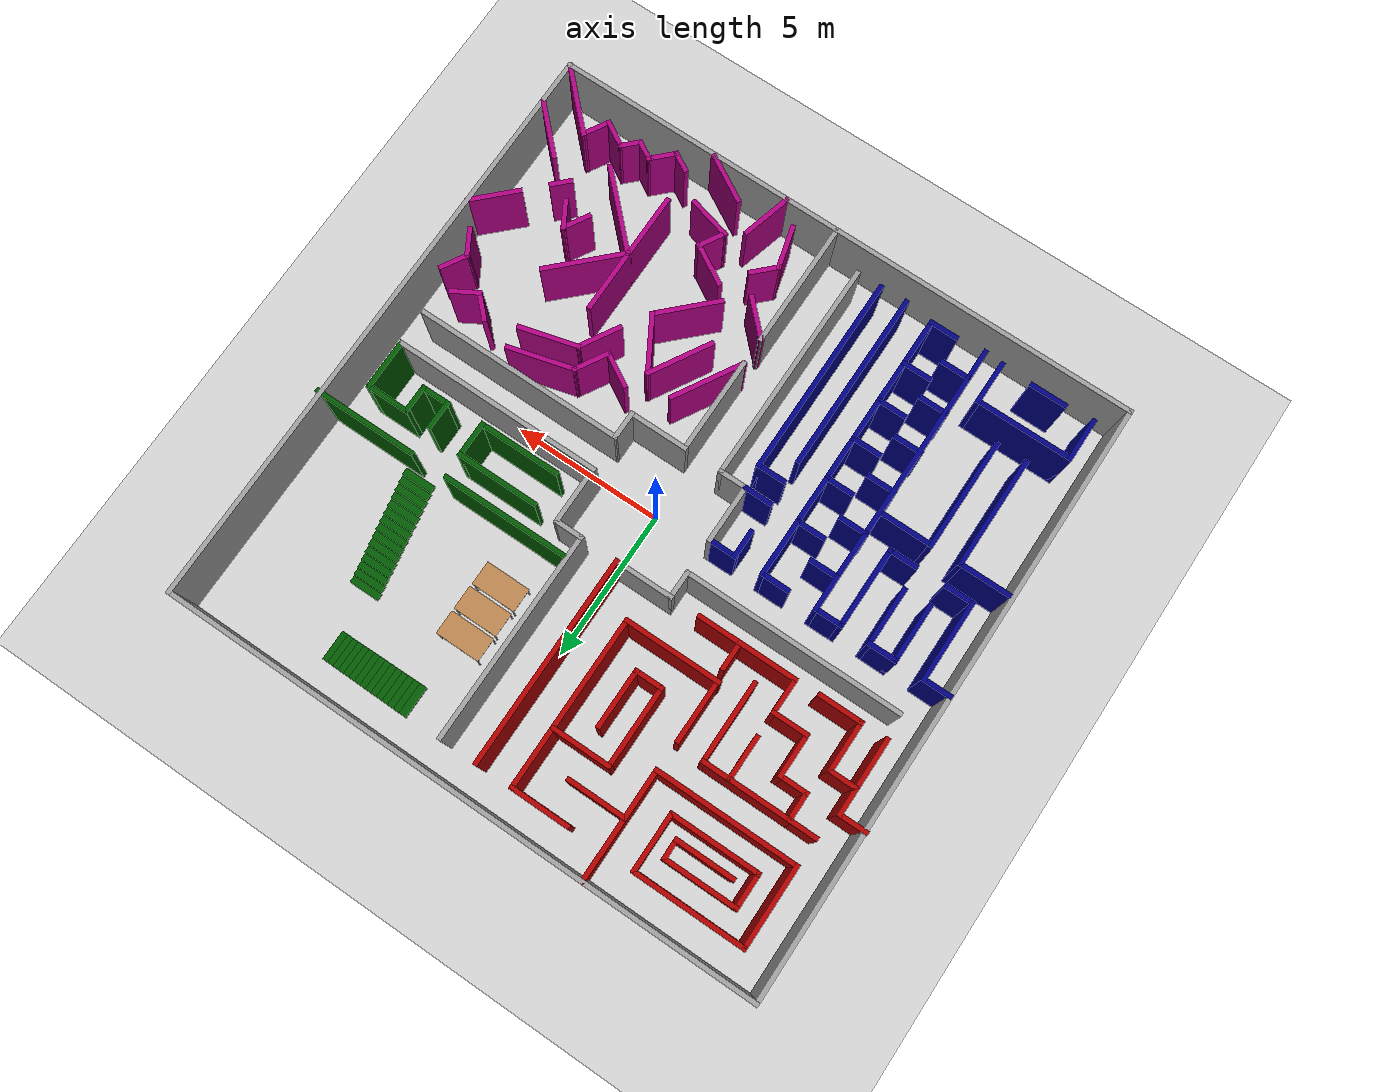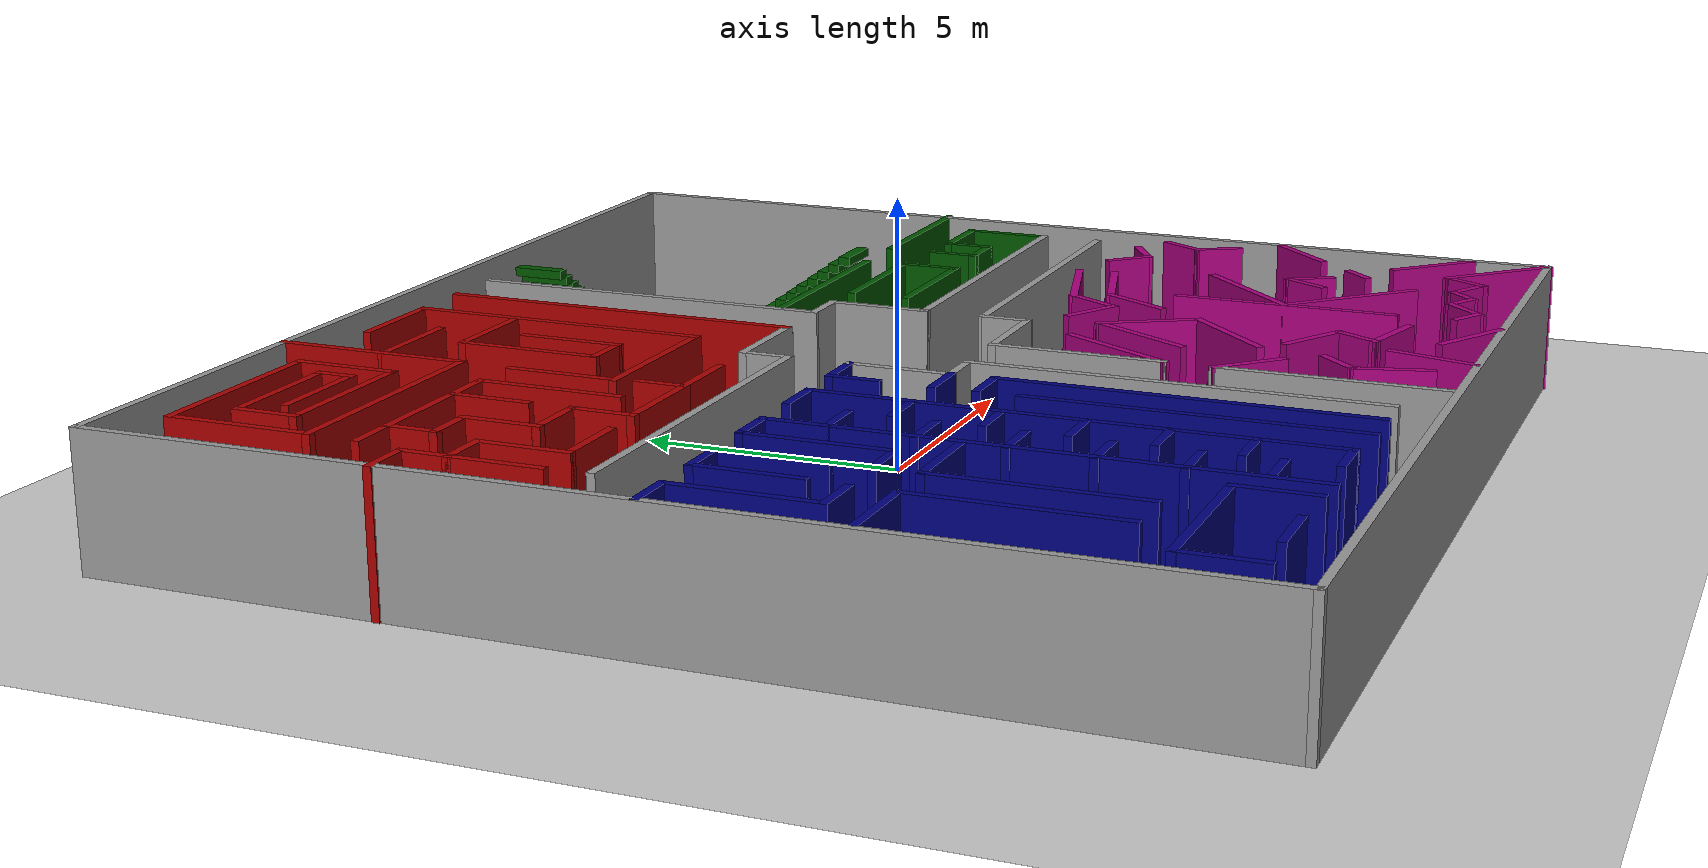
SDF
<sdf version="1.7">
 <world name="default">
  <model name="ground_plane">
   <static>1</static>
   <link name="link">
    <collision name="collision">
     <geometry><plane><normal>0 0 1</normal><size>100 100</size></plane></geometry>
     <surface><friction><ode><mu>100</mu><mu2>50</mu2></ode></friction></surface>
    </collision>
    <visual name="visual">
     <cast_shadows>0</cast_shadows>
     <geometry><plane><normal>0 0 1</normal><size>100 100</size></plane></geometry>
     <material>
      <script><uri>file://media/materials/scripts/gazebo.material</uri><name>Gazebo/Grey</name></script>
     </material>
    </visual>
   </link>
  </model>
  <light name="sun" type="directional">
   <pose>0 0 10 0 -0 0</pose>
   <diffuse>0.8 0.8 0.8 1</diffuse>
   <specular>0.2 0.2 0.2 1</specular>
   <attenuation>
    <range>1000</range>
    <constant>0.9</constant>
    <linear>0.01</linear>
    <quadratic>0.001</quadratic>
   </attenuation>
   <direction>-0.5 0.1 -0.9</direction>
   <spot><inner_angle>0</inner_angle><outer_angle>0</outer_angle><falloff>0</falloff></spot>
  </light>
  <scene><shadows>0</shadows><ambient>0.4 0.4 0.4 1</ambient><background>0.7 0.7 0.7 1</background></scene>
  <physics type="ode">
   <real_time_update_rate>1000</real_time_update_rate>
   <max_step_size>0.001</max_step_size>
   <real_time_factor>1</real_time_factor>
   <ode>
    <solver>
     <type>quick</type>
     <iters>150</iters>
     <precon_iters>0</precon_iters>
     <sor>1.4</sor>
     <use_dynamic_moi_rescaling>1</use_dynamic_moi_rescaling>
    </solver>
    <constraints>
     <cfm>1e-05</cfm>
     <erp>0.2</erp>
     <contact_max_correcting_vel>2000</contact_max_correcting_vel>
     <contact_surface_layer>0.01</contact_surface_layer>
    </constraints>
   </ode>
  </physics>
  <gravity>0 0 -9.8</gravity>
  <magnetic_field>6e-06 2.3e-05 -4.2e-05</magnetic_field>
  <atmosphere type="adiabatic"/>
  <spherical_coordinates>
   <surface_model>EARTH_WGS84</surface_model>
   <latitude_deg>0</latitude_deg>
   <longitude_deg>0</longitude_deg>
   <elevation>0</elevation>
   <heading_deg>0</heading_deg>
  </spherical_coordinates>
  <model name="labyrinthe">
   <pose>-0.001061 -0.00174 0 0 -0 0</pose>
   <link name="Stairs_0">
    <visual name="Stairs_0_Visual_0">
     <pose>5.96244 6.62392 0.083333 0 -0 0</pose>
     <geometry><box><size>1 0.233333 0.166667</size></box></geometry>
     <material>
      <script><uri>file://media/materials/scripts/gazebo.material</uri><name>Gazebo/Grey</name></script>
      <ambient>0 0.333333 0 1</ambient>
     </material>
     <meta><layer>0</layer></meta>
    </visual>
    <collision name="Stairs_0_Collision_0">
     <geometry><box><size>1 0.233333 0.166667</size></box></geometry>
     <pose>5.96244 6.62392 0.083333 0 -0 0</pose>
    </collision>
    <visual name="Stairs_0_Visual_1">
     <pose>5.96244 6.39059 0.25 0 -0 0</pose>
     <geometry><box><size>1 0.233333 0.166667</size></box></geometry>
     <material>
      <script><uri>file://media/materials/scripts/gazebo.material</uri><name>Gazebo/Grey</name></script>
      <ambient>0 0.333333 0 1</ambient>
     </material>
     <meta><layer>0</layer></meta>
    </visual>
    <collision name="Stairs_0_Collision_1">
     <geometry><box><size>1 0.233333 0.166667</size></box></geometry>
     <pose>5.96244 6.39059 0.25 0 -0 0</pose>
    </collision>
    <visual name="Stairs_0_Visual_2">
     <pose>5.96244 6.15725 0.416667 0 -0 0</pose>
     <geometry><box><size>1 0.233333 0.166667</size></box></geometry>
     <material>
      <script><uri>file://media/materials/scripts/gazebo.material</uri><name>Gazebo/Grey</name></script>
      <ambient>0 0.333333 0 1</ambient>
     </material>
     <meta><layer>0</layer></meta>
    </visual>
    <collision name="Stairs_0_Collision_2">
     <geometry><box><size>1 0.233333 0.166667</size></box></geometry>
     <pose>5.96244 6.15725 0.416667 0 -0 0</pose>
    </collision>
    <visual name="Stairs_0_Visual_3">
     <pose>5.96244 5.92392 0.583333 0 -0 0</pose>
     <geometry><box><size>1 0.233333 0.166667</size></box></geometry>
     <material>
      <script><uri>file://media/materials/scripts/gazebo.material</uri><name>Gazebo/Grey</name></script>
      <ambient>0 0.333333 0 1</ambient>
     </material>
     <meta><layer>0</layer></meta>
    </visual>
    <collision name="Stairs_0_Collision_3">
     <geometry><box><size>1 0.233333 0.166667</size></box></geometry>
     <pose>5.96244 5.92392 0.583333 0 -0 0</pose>
    </collision>
    <visual name="Stairs_0_Visual_4">
     <pose>5.96244 5.69059 0.75 0 -0 0</pose>
     <geometry><box><size>1 0.233333 0.166667</size></box></geometry>
     <material>
      <script><uri>file://media/materials/scripts/gazebo.material</uri><name>Gazebo/Grey</name></script>
      <ambient>0 0.333333 0 1</ambient>
     </material>
     <meta><layer>0</layer></meta>
    </visual>
    <collision name="Stairs_0_Collision_4">
     <geometry><box><size>1 0.233333 0.166667</size></box></geometry>
     <pose>5.96244 5.69059 0.75 0 -0 0</pose>
    </collision>
    <visual name="Stairs_0_Visual_5">
     <pose>5.96244 5.45725 0.916667 0 -0 0</pose>
     <geometry><box><size>1 0.233333 0.166667</size></box></geometry>
     <material>
      <script><uri>file://media/materials/scripts/gazebo.material</uri><name>Gazebo/Grey</name></script>
      <ambient>0 0.333333 0 1</ambient>
     </material>
     <meta><layer>0</layer></meta>
    </visual>
    <collision name="Stairs_0_Collision_5">
     <geometry><box><size>1 0.233333 0.166667</size></box></geometry>
     <pose>5.96244 5.45725 0.916667 0 -0 0</pose>
    </collision>
    <visual name="Stairs_0_Visual_6">
     <pose>5.96244 5.22392 1.08333 0 -0 0</pose>
     <geometry><box><size>1 0.233333 0.166667</size></box></geometry>
     <material>
      <script><uri>file://media/materials/scripts/gazebo.material</uri><name>Gazebo/Grey</name></script>
      <ambient>0 0.333333 0 1</ambient>
     </material>
     <meta><layer>0</layer></meta>
    </visual>
    <collision name="Stairs_0_Collision_6">
     <geometry><box><size>1 0.233333 0.166667</size></box></geometry>
     <pose>5.96244 5.22392 1.08333 0 -0 0</pose>
    </collision>
    <visual name="Stairs_0_Visual_7">
     <pose>5.96244 4.99059 1.25 0 -0 0</pose>
     <geometry><box><size>1 0.233333 0.166667</size></box></geometry>
     <material>
      <script><uri>file://media/materials/scripts/gazebo.material</uri><name>Gazebo/Grey</name></script>
      <ambient>0 0.333333 0 1</ambient>
     </material>
     <meta><layer>0</layer></meta>
    </visual>
    <collision name="Stairs_0_Collision_7">
     <geometry><box><size>1 0.233333 0.166667</size></box></geometry>
     <pose>5.96244 4.99059 1.25 0 -0 0</pose>
    </collision>
    <visual name="Stairs_0_Visual_8">
     <pose>5.96244 4.75725 1.41667 0 -0 0</pose>
     <geometry><box><size>1 0.233333 0.166667</size></box></geometry>
     <material>
      <script><uri>file://media/materials/scripts/gazebo.material</uri><name>Gazebo/Grey</name></script>
      <ambient>0 0.333333 0 1</ambient>
     </material>
     <meta><layer>0</layer></meta>
    </visual>
    <collision name="Stairs_0_Collision_8">
     <geometry><box><size>1 0.233333 0.166667</size></box></geometry>
     <pose>5.96244 4.75725 1.41667 0 -0 0</pose>
    </collision>
    <visual name="Stairs_0_Visual_9">
     <pose>5.96244 4.52392 1.58333 0 -0 0</pose>
     <geometry><box><size>1 0.233333 0.166667</size></box></geometry>
     <material>
      <script><uri>file://media/materials/scripts/gazebo.material</uri><name>Gazebo/Grey</name></script>
      <ambient>0 0.333333 0 1</ambient>
     </material>
     <meta><layer>0</layer></meta>
    </visual>
    <collision name="Stairs_0_Collision_9">
     <geometry><box><size>1 0.233333 0.166667</size></box></geometry>
     <pose>5.96244 4.52392 1.58333 0 -0 0</pose>
    </collision>
    <visual name="Stairs_0_Visual_10">
     <pose>5.96244 4.29059 1.75 0 -0 0</pose>
     <geometry><box><size>1 0.233333 0.166667</size></box></geometry>
     <material>
      <script><uri>file://media/materials/scripts/gazebo.material</uri><name>Gazebo/Grey</name></script>
      <ambient>0 0.333333 0 1</ambient>
     </material>
     <meta><layer>0</layer></meta>
    </visual>
    <collision name="Stairs_0_Collision_10">
     <geometry><box><size>1 0.233333 0.166667</size></box></geometry>
     <pose>5.96244 4.29059 1.75 0 -0 0</pose>
    </collision>
    <visual name="Stairs_0_Visual_11">
     <pose>5.96244 4.05725 1.91667 0 -0 0</pose>
     <geometry><box><size>1 0.233333 0.166667</size></box></geometry>
     <material>
      <script><uri>file://media/materials/scripts/gazebo.material</uri><name>Gazebo/Grey</name></script>
      <ambient>0 0.333333 0 1</ambient>
     </material>
     <meta><layer>0</layer></meta>
    </visual>
    <collision name="Stairs_0_Collision_11">
     <geometry><box><size>1 0.233333 0.166667</size></box></geometry>
     <pose>5.96244 4.05725 1.91667 0 -0 0</pose>
    </collision>
    <visual name="Stairs_0_Visual_12">
     <pose>5.96244 3.82392 2.08333 0 -0 0</pose>
     <geometry><box><size>1 0.233333 0.166667</size></box></geometry>
     <material>
      <script><uri>file://media/materials/scripts/gazebo.material</uri><name>Gazebo/Grey</name></script>
      <ambient>0 0.333333 0 1</ambient>
     </material>
     <meta><layer>0</layer></meta>
    </visual>
    <collision name="Stairs_0_Collision_12">
     <geometry><box><size>1 0.233333 0.166667</size></box></geometry>
     <pose>5.96244 3.82392 2.08333 0 -0 0</pose>
    </collision>
    <visual name="Stairs_0_Visual_13">
     <pose>5.96244 3.59059 2.25 0 -0 0</pose>
     <geometry><box><size>1 0.233333 0.166667</size></box></geometry>
     <material>
      <script><uri>file://media/materials/scripts/gazebo.material</uri><name>Gazebo/Grey</name></script>
      <ambient>0 0.333333 0 1</ambient>
     </material>
     <meta><layer>0</layer></meta>
    </visual>
    <collision name="Stairs_0_Collision_13">
     <geometry><box><size>1 0.233333 0.166667</size></box></geometry>
     <pose>5.96244 3.59059 2.25 0 -0 0</pose>
    </collision>
    <visual name="Stairs_0_Visual_14">
     <pose>5.96244 3.35725 2.41667 0 -0 0</pose>
     <geometry><box><size>1 0.233333 0.166667</size></box></geometry>
     <material>
      <script><uri>file://media/materials/scripts/gazebo.material</uri><name>Gazebo/Grey</name></script>
      <ambient>0 0.333333 0 1</ambient>
     </material>
     <meta><layer>0</layer></meta>
    </visual>
    <collision name="Stairs_0_Collision_14">
     <geometry><box><size>1 0.233333 0.166667</size></box></geometry>
     <pose>5.96244 3.35725 2.41667 0 -0 0</pose>
    </collision>
   </link>
   <link name="Stairs_1">
    <visual name="Stairs_1_Visual_0">
     <pose>5.63847 8.54811 0.083333 0 -0 -1.5708</pose>
     <geometry><box><size>1 0.233333 0.166667</size></box></geometry>
     <material>
      <script><uri>file://media/materials/scripts/gazebo.material</uri><name>Gazebo/Grey</name></script>
      <ambient>0 0.333333 0 1</ambient>
     </material>
     <meta><layer>0</layer></meta>
    </visual>
    <collision name="Stairs_1_Collision_0">
     <geometry><box><size>1 0.233333 0.166667</size></box></geometry>
     <pose>5.63847 8.54811 0.083333 0 -0 -1.5708</pose>
    </collision>
    <visual name="Stairs_1_Visual_1">
     <pose>5.40514 8.54811 0.25 0 -0 -1.5708</pose>
     <geometry><box><size>1 0.233333 0.166667</size></box></geometry>
     <material>
      <script><uri>file://media/materials/scripts/gazebo.material</uri><name>Gazebo/Grey</name></script>
      <ambient>0 0.333333 0 1</ambient>
     </material>
     <meta><layer>0</layer></meta>
    </visual>
    <collision name="Stairs_1_Collision_1">
     <geometry><box><size>1 0.233333 0.166667</size></box></geometry>
     <pose>5.40514 8.54811 0.25 0 -0 -1.5708</pose>
    </collision>
    <visual name="Stairs_1_Visual_2">
     <pose>5.1718 8.54811 0.416667 0 -0 -1.5708</pose>
     <geometry><box><size>1 0.233333 0.166667</size></box></geometry>
     <material>
      <script><uri>file://media/materials/scripts/gazebo.material</uri><name>Gazebo/Grey</name></script>
      <ambient>0 0.333333 0 1</ambient>
     </material>
     <meta><layer>0</layer></meta>
    </visual>
    <collision name="Stairs_1_Collision_2">
     <geometry><box><size>1 0.233333 0.166667</size></box></geometry>
     <pose>5.1718 8.54811 0.416667 0 -0 -1.5708</pose>
    </collision>
    <visual name="Stairs_1_Visual_3">
     <pose>4.93847 8.54811 0.583333 0 -0 -1.5708</pose>
     <geometry><box><size>1 0.233333 0.166667</size></box></geometry>
     <material>
      <script><uri>file://media/materials/scripts/gazebo.material</uri><name>Gazebo/Grey</name></script>
      <ambient>0 0.333333 0 1</ambient>
     </material>
     <meta><layer>0</layer></meta>
    </visual>
    <collision name="Stairs_1_Collision_3">
     <geometry><box><size>1 0.233333 0.166667</size></box></geometry>
     <pose>4.93847 8.54811 0.583333 0 -0 -1.5708</pose>
    </collision>
    <visual name="Stairs_1_Visual_4">
     <pose>4.70514 8.54811 0.75 0 -0 -1.5708</pose>
     <geometry><box><size>1 0.233333 0.166667</size></box></geometry>
     <material>
      <script><uri>file://media/materials/scripts/gazebo.material</uri><name>Gazebo/Grey</name></script>
      <ambient>0 0.333333 0 1</ambient>
     </material>
     <meta><layer>0</layer></meta>
    </visual>
    <collision name="Stairs_1_Collision_4">
     <geometry><box><size>1 0.233333 0.166667</size></box></geometry>
     <pose>4.70514 8.54811 0.75 0 -0 -1.5708</pose>
    </collision>
    <visual name="Stairs_1_Visual_5">
     <pose>4.4718 8.54811 0.916667 0 -0 -1.5708</pose>
     <geometry><box><size>1 0.233333 0.166667</size></box></geometry>
     <material>
      <script><uri>file://media/materials/scripts/gazebo.material</uri><name>Gazebo/Grey</name></script>
      <ambient>0 0.333333 0 1</ambient>
     </material>
     <meta><layer>0</layer></meta>
    </visual>
    <collision name="Stairs_1_Collision_5">
     <geometry><box><size>1 0.233333 0.166667</size></box></geometry>
     <pose>4.4718 8.54811 0.916667 0 -0 -1.5708</pose>
    </collision>
    <visual name="Stairs_1_Visual_6">
     <pose>4.23847 8.54811 1.08333 0 -0 -1.5708</pose>
     <geometry><box><size>1 0.233333 0.166667</size></box></geometry>
     <material>
      <script><uri>file://media/materials/scripts/gazebo.material</uri><name>Gazebo/Grey</name></script>
      <ambient>0 0.333333 0 1</ambient>
     </material>
     <meta><layer>0</layer></meta>
    </visual>
    <collision name="Stairs_1_Collision_6">
     <geometry><box><size>1 0.233333 0.166667</size></box></geometry>
     <pose>4.23847 8.54811 1.08333 0 -0 -1.5708</pose>
    </collision>
    <visual name="Stairs_1_Visual_7">
     <pose>4.00514 8.54811 1.25 0 -0 -1.5708</pose>
     <geometry><box><size>1 0.233333 0.166667</size></box></geometry>
     <material>
      <script><uri>file://media/materials/scripts/gazebo.material</uri><name>Gazebo/Grey</name></script>
      <ambient>0 0.333333 0 1</ambient>
     </material>
     <meta><layer>0</layer></meta>
    </visual>
    <collision name="Stairs_1_Collision_7">
     <geometry><box><size>1 0.233333 0.166667</size></box></geometry>
     <pose>4.00514 8.54811 1.25 0 -0 -1.5708</pose>
    </collision>
    <visual name="Stairs_1_Visual_8">
     <pose>3.77181 8.54811 1.41667 0 -0 -1.5708</pose>
     <geometry><box><size>1 0.233333 0.166667</size></box></geometry>
     <material>
      <script><uri>file://media/materials/scripts/gazebo.material</uri><name>Gazebo/Grey</name></script>
      <ambient>0 0.333333 0 1</ambient>
     </material>
     <meta><layer>0</layer></meta>
    </visual>
    <collision name="Stairs_1_Collision_8">
     <geometry><box><size>1 0.233333 0.166667</size></box></geometry>
     <pose>3.77181 8.54811 1.41667 0 -0 -1.5708</pose>
    </collision>
    <visual name="Stairs_1_Visual_9">
     <pose>3.53847 8.54811 1.58333 0 -0 -1.5708</pose>
     <geometry><box><size>1 0.233333 0.166667</size></box></geometry>
     <material>
      <script><uri>file://media/materials/scripts/gazebo.material</uri><name>Gazebo/Grey</name></script>
      <ambient>0 0.333333 0 1</ambient>
     </material>
     <meta><layer>0</layer></meta>
    </visual>
    <collision name="Stairs_1_Collision_9">
     <geometry><box><size>1 0.233333 0.166667</size></box></geometry>
     <pose>3.53847 8.54811 1.58333 0 -0 -1.5708</pose>
    </collision>
    <visual name="Stairs_1_Visual_10">
     <pose>3.30514 8.54811 1.75 0 -0 -1.5708</pose>
     <geometry><box><size>1 0.233333 0.166667</size></box></geometry>
     <material>
      <script><uri>file://media/materials/scripts/gazebo.material</uri><name>Gazebo/Grey</name></script>
      <ambient>0 0.333333 0 1</ambient>
     </material>
     <meta><layer>0</layer></meta>
    </visual>
    <collision name="Stairs_1_Collision_10">
     <geometry><box><size>1 0.233333 0.166667</size></box></geometry>
     <pose>3.30514 8.54811 1.75 0 -0 -1.5708</pose>
    </collision>
    <visual name="Stairs_1_Visual_11">
     <pose>3.0718 8.54811 1.91667 0 -0 -1.5708</pose>
     <geometry><box><size>1 0.233333 0.166667</size></box></geometry>
     <material>
      <script><uri>file://media/materials/scripts/gazebo.material</uri><name>Gazebo/Grey</name></script>
      <ambient>0 0.333333 0 1</ambient>
     </material>
     <meta><layer>0</layer></meta>
    </visual>
    <collision name="Stairs_1_Collision_11">
     <geometry><box><size>1 0.233333 0.166667</size></box></geometry>
     <pose>3.0718 8.54811 1.91667 0 -0 -1.5708</pose>
    </collision>
    <visual name="Stairs_1_Visual_12">
     <pose>2.83847 8.54811 2.08333 0 -0 -1.5708</pose>
     <geometry><box><size>1 0.233333 0.166667</size></box></geometry>
     <material>
      <script><uri>file://media/materials/scripts/gazebo.material</uri><name>Gazebo/Grey</name></script>
      <ambient>0 0.333333 0 1</ambient>
     </material>
     <meta><layer>0</layer></meta>
    </visual>
    <collision name="Stairs_1_Collision_12">
     <geometry><box><size>1 0.233333 0.166667</size></box></geometry>
     <pose>2.83847 8.54811 2.08333 0 -0 -1.5708</pose>
    </collision>
    <visual name="Stairs_1_Visual_13">
     <pose>2.60514 8.54811 2.25 0 -0 -1.5708</pose>
     <geometry><box><size>1 0.233333 0.166667</size></box></geometry>
     <material>
      <script><uri>file://media/materials/scripts/gazebo.material</uri><name>Gazebo/Grey</name></script>
      <ambient>0 0.333333 0 1</ambient>
     </material>
     <meta><layer>0</layer></meta>
    </visual>
    <collision name="Stairs_1_Collision_13">
     <geometry><box><size>1 0.233333 0.166667</size></box></geometry>
     <pose>2.60514 8.54811 2.25 0 -0 -1.5708</pose>
    </collision>
    <visual name="Stairs_1_Visual_14">
     <pose>2.3718 8.54811 2.41667 0 -0 -1.5708</pose>
     <geometry><box><size>1 0.233333 0.166667</size></box></geometry>
     <material>
      <script><uri>file://media/materials/scripts/gazebo.material</uri><name>Gazebo/Grey</name></script>
      <ambient>0 0.333333 0 1</ambient>
     </material>
     <meta><layer>0</layer></meta>
    </visual>
    <collision name="Stairs_1_Collision_14">
     <geometry><box><size>1 0.233333 0.166667</size></box></geometry>
     <pose>2.3718 8.54811 2.41667 0 -0 -1.5708</pose>
    </collision>
   </link>
   <link name="Wall_100">
    <collision name="Wall_100_Collision">
     <geometry><box><size>1 0.15 2.5</size></box></geometry>
     <pose>0 0 1.25 0 -0 0</pose>
    </collision>
    <visual name="Wall_100_Visual">
     <pose>0 0 1.25 0 -0 0</pose>
     <geometry><box><size>1 0.15 2.5</size></box></geometry>
     <material>
      <script><uri>file://media/materials/scripts/gazebo.material</uri><name>Gazebo/Grey</name></script>
      <ambient>0.666667 0 0 1</ambient>
     </material>
     <meta><layer>0</layer></meta>
    </visual>
    <pose>-4.27476 2.53254 0 0 -0 1.5708</pose>
   </link>
   <link name="Wall_102">
    <collision name="Wall_102_Collision">
     <geometry><box><size>2 0.15 2.5</size></box></geometry>
     <pose>0 0 1.25 0 -0 0</pose>
    </collision>
    <visual name="Wall_102_Visual">
     <pose>0 0 1.25 0 -0 0</pose>
     <geometry><box><size>2 0.15 2.5</size></box></geometry>
     <material>
      <script><uri>file://media/materials/scripts/gazebo.material</uri><name>Gazebo/Grey</name></script>
      <ambient>0.666667 0 0 1</ambient>
     </material>
     <meta><layer>0</layer></meta>
    </visual>
    <pose>-5.19976 2.10754 0 0 -0 3.14159</pose>
   </link>
   <link name="Wall_103">
    <collision name="Wall_103_Collision">
     <geometry><box><size>1.25 0.15 2.5</size></box></geometry>
     <pose>0 0 1.25 0 -0 0</pose>
    </collision>
    <visual name="Wall_103_Visual">
     <pose>0 0 1.25 0 -0 0</pose>
     <geometry><box><size>1.25 0.15 2.5</size></box></geometry>
     <material>
      <script><uri>file://media/materials/scripts/gazebo.material</uri><name>Gazebo/Grey</name></script>
      <ambient>0.666667 0 0 1</ambient>
     </material>
     <meta><layer>0</layer></meta>
    </visual>
    <pose>-6.12476 2.65754 0 0 -0 1.5708</pose>
   </link>
   <link name="Wall_104">
    <collision name="Wall_104_Collision">
     <geometry><box><size>1.25 0.15 2.5</size></box></geometry>
     <pose>0 0 1.25 0 -0 0</pose>
    </collision>
    <visual name="Wall_104_Visual">
     <pose>0 0 1.25 0 -0 0</pose>
     <geometry><box><size>1.25 0.15 2.5</size></box></geometry>
     <material>
      <script><uri>file://media/materials/scripts/gazebo.material</uri><name>Gazebo/Grey</name></script>
      <ambient>0.666667 0 0 1</ambient>
     </material>
     <meta><layer>0</layer></meta>
    </visual>
    <pose>-6.67476 3.20754 0 0 -0 3.14159</pose>
   </link>
   <link name="Wall_105">
    <collision name="Wall_105_Collision">
     <geometry><box><size>1.5 0.15 2.5</size></box></geometry>
     <pose>0 0 1.25 0 -0 0</pose>
    </collision>
    <visual name="Wall_105_Visual">
     <pose>0 0 1.25 0 -0 0</pose>
     <geometry><box><size>1.5 0.15 2.5</size></box></geometry>
     <material>
      <script><uri>file://media/materials/scripts/gazebo.material</uri><name>Gazebo/Grey</name></script>
      <ambient>0.666667 0 0 1</ambient>
     </material>
     <meta><layer>0</layer></meta>
    </visual>
    <pose>-7.22476 3.88254 0 0 -0 1.5708</pose>
   </link>
   <link name="Wall_106">
    <collision name="Wall_106_Collision">
     <geometry><box><size>1 0.15 2.5</size></box></geometry>
     <pose>0 0 1.25 0 -0 0</pose>
    </collision>
    <visual name="Wall_106_Visual">
     <pose>0 0 1.25 0 -0 0</pose>
     <geometry><box><size>1 0.15 2.5</size></box></geometry>
     <material>
      <script><uri>file://media/materials/scripts/gazebo.material</uri><name>Gazebo/Grey</name></script>
      <ambient>0.666667 0 0 1</ambient>
     </material>
     <meta><layer>0</layer></meta>
    </visual>
    <pose>-7.64976 4.55754 0 0 -0 3.14159</pose>
   </link>
   <link name="Wall_107">
    <collision name="Wall_107_Collision">
     <geometry><box><size>1 0.15 2.5</size></box></geometry>
     <pose>0 0 1.25 0 -0 0</pose>
    </collision>
    <visual name="Wall_107_Visual">
     <pose>0 0 1.25 0 -0 0</pose>
     <geometry><box><size>1 0.15 2.5</size></box></geometry>
     <material>
      <script><uri>file://media/materials/scripts/gazebo.material</uri><name>Gazebo/Grey</name></script>
      <ambient>0.666667 0 0 1</ambient>
     </material>
     <meta><layer>0</layer></meta>
    </visual>
    <pose>-8.07476 4.98254 0 0 -0 1.5708</pose>
   </link>
   <link name="Wall_108">
    <collision name="Wall_108_Collision">
     <geometry><box><size>1 0.15 2.5</size></box></geometry>
     <pose>0 0 1.25 0 -0 0</pose>
    </collision>
    <visual name="Wall_108_Visual">
     <pose>0 0 1.25 0 -0 0</pose>
     <geometry><box><size>1 0.15 2.5</size></box></geometry>
     <material>
      <script><uri>file://media/materials/scripts/gazebo.material</uri><name>Gazebo/Grey</name></script>
      <ambient>0.666667 0 0 1</ambient>
     </material>
     <meta><layer>0</layer></meta>
    </visual>
    <pose>-8.51299 5.42076 0 0 -0 3.14159</pose>
   </link>
   <link name="Wall_110">
    <collision name="Wall_110_Collision">
     <geometry><box><size>1 0.15 2.5</size></box></geometry>
     <pose>0 0 1.25 0 -0 0</pose>
    </collision>
    <visual name="Wall_110_Visual">
     <pose>0 0 1.25 0 -0 0</pose>
     <geometry><box><size>1 0.15 2.5</size></box></geometry>
     <material>
      <script><uri>file://media/materials/scripts/gazebo.material</uri><name>Gazebo/Grey</name></script>
      <ambient>0.666667 0 0 1</ambient>
     </material>
     <meta><layer>0</layer></meta>
    </visual>
    <pose>-9.56191 4.52771 0 0 -0 0</pose>
   </link>
   <link name="Wall_111">
    <collision name="Wall_111_Collision">
     <geometry><box><size>1 0.15 2.5</size></box></geometry>
     <pose>0 0 1.25 0 -0 0</pose>
    </collision>
    <visual name="Wall_111_Visual">
     <pose>0 0 1.25 0 -0 0</pose>
     <geometry><box><size>1 0.15 2.5</size></box></geometry>
     <material>
      <script><uri>file://media/materials/scripts/gazebo.material</uri><name>Gazebo/Grey</name></script>
      <ambient>0.666667 0 0 1</ambient>
     </material>
     <meta><layer>0</layer></meta>
    </visual>
    <pose>-9.13691 4.10271 0 0 -0 -1.5708</pose>
   </link>
   <link name="Wall_112">
    <collision name="Wall_112_Collision">
     <geometry><box><size>1 0.15 2.5</size></box></geometry>
     <pose>0 0 1.25 0 -0 0</pose>
    </collision>
    <visual name="Wall_112_Visual">
     <pose>0 0 1.25 0 -0 0</pose>
     <geometry><box><size>1 0.15 2.5</size></box></geometry>
     <material>
      <script><uri>file://media/materials/scripts/gazebo.material</uri><name>Gazebo/Grey</name></script>
      <ambient>0.666667 0 0 1</ambient>
     </material>
     <meta><layer>0</layer></meta>
    </visual>
    <pose>-8.71191 3.67771 0 0 -0 0</pose>
   </link>
   <link name="Wall_113">
    <collision name="Wall_113_Collision">
     <geometry><box><size>1.75 0.15 2.5</size></box></geometry>
     <pose>0 0 1.25 0 -0 0</pose>
    </collision>
    <visual name="Wall_113_Visual">
     <pose>0 0 1.25 0 -0 0</pose>
     <geometry><box><size>1.75 0.15 2.5</size></box></geometry>
     <material>
      <script><uri>file://media/materials/scripts/gazebo.material</uri><name>Gazebo/Grey</name></script>
      <ambient>0.666667 0 0 1</ambient>
     </material>
     <meta><layer>0</layer></meta>
    </visual>
    <pose>-8.28691 2.87771 0 0 -0 -1.5708</pose>
   </link>
   <link name="Wall_114">
    <collision name="Wall_114_Collision">
     <geometry><box><size>1.5 0.15 2.5</size></box></geometry>
     <pose>0 0 1.25 0 -0 0</pose>
    </collision>
    <visual name="Wall_114_Visual">
     <pose>0 0 1.25 0 -0 0</pose>
     <geometry><box><size>1.5 0.15 2.5</size></box></geometry>
     <material>
      <script><uri>file://media/materials/scripts/gazebo.material</uri><name>Gazebo/Grey</name></script>
      <ambient>0.666667 0 0 1</ambient>
     </material>
     <meta><layer>0</layer></meta>
    </visual>
    <pose>-7.61191 2.07771 0 0 -0 0</pose>
   </link>
   <link name="Wall_116">
    <collision name="Wall_116_Collision">
     <geometry><box><size>1.75 0.15 2.5</size></box></geometry>
     <pose>0 0 1.25 0 -0 0</pose>
    </collision>
    <visual name="Wall_116_Visual">
     <pose>0 0 1.25 0 -0 0</pose>
     <geometry><box><size>1.75 0.15 2.5</size></box></geometry>
     <material>
      <script><uri>file://media/materials/scripts/gazebo.material</uri><name>Gazebo/Grey</name></script>
      <ambient>0.666667 0 0 1</ambient>
     </material>
     <meta><layer>0</layer></meta>
    </visual>
    <pose>-9.13691 2.87771 0 0 -0 -1.5708</pose>
   </link>
   <link name="Wall_118">
    <collision name="Wall_118_Collision">
     <geometry><box><size>3 0.15 2.5</size></box></geometry>
     <pose>0 0 1.25 0 -0 0</pose>
    </collision>
    <visual name="Wall_118_Visual">
     <pose>0 0 1.25 0 -0 0</pose>
     <geometry><box><size>3 0.15 2.5</size></box></geometry>
     <material>
      <script><uri>file://media/materials/scripts/gazebo.material</uri><name>Gazebo/Grey</name></script>
      <ambient>0.666667 0 0 1</ambient>
     </material>
     <meta><layer>0</layer></meta>
    </visual>
    <pose>-6.66299 5.42076 0 0 -0 0</pose>
   </link>
   <link name="Wall_119">
    <collision name="Wall_119_Collision">
     <geometry><box><size>2.75 0.15 2.5</size></box></geometry>
     <pose>0 0 1.25 0 -0 0</pose>
    </collision>
    <visual name="Wall_119_Visual">
     <pose>0 0 1.25 0 -0 0</pose>
     <geometry><box><size>2.75 0.15 2.5</size></box></geometry>
     <material>
      <script><uri>file://media/materials/scripts/gazebo.material</uri><name>Gazebo/Grey</name></script>
      <ambient>0.666667 0 0 1</ambient>
     </material>
     <meta><layer>0</layer></meta>
    </visual>
    <pose>-5.23799 4.12076 0 0 -0 -1.5708</pose>
   </link>
   <link name="Wall_121">
    <collision name="Wall_121_Collision">
     <geometry><box><size>1.5 0.15 2.5</size></box></geometry>
     <pose>0 0 1.25 0 -0 0</pose>
    </collision>
    <visual name="Wall_121_Visual">
     <pose>0 0 1.25 0 -0 0</pose>
     <geometry><box><size>1.5 0.15 2.5</size></box></geometry>
     <material>
      <script><uri>file://media/materials/scripts/gazebo.material</uri><name>Gazebo/Grey</name></script>
      <ambient>0.666667 0 0 1</ambient>
     </material>
     <meta><layer>0</layer></meta>
    </visual>
    <pose>-6.11199 4.71234 0 0 -0 -1.5708</pose>
   </link>
   <link name="Wall_123">
    <collision name="Wall_123_Collision">
     <geometry><box><size>1 0.15 2.5</size></box></geometry>
     <pose>0 0 1.25 0 -0 0</pose>
    </collision>
    <visual name="Wall_123_Visual">
     <pose>0 0 1.25 0 -0 0</pose>
     <geometry><box><size>1 0.15 2.5</size></box></geometry>
     <material>
      <script><uri>file://media/materials/scripts/gazebo.material</uri><name>Gazebo/Grey</name></script>
      <ambient>0 0 0.498039 1</ambient>
     </material>
     <meta><layer>0</layer></meta>
    </visual>
    <pose>-2.35877 0.113732 0 0 -0 3.14159</pose>
   </link>
   <link name="Wall_124">
    <collision name="Wall_124_Collision">
     <geometry><box><size>1 0.15 2.5</size></box></geometry>
     <pose>0 0 1.25 0 -0 0</pose>
    </collision>
    <visual name="Wall_124_Visual">
     <pose>0 0 1.25 0 -0 0</pose>
     <geometry><box><size>1 0.15 2.5</size></box></geometry>
     <material>
      <script><uri>file://media/materials/scripts/gazebo.material</uri><name>Gazebo/Grey</name></script>
      <ambient>0 0 0.498039 1</ambient>
     </material>
     <meta><layer>0</layer></meta>
    </visual>
    <pose>-2.78376 -0.311268 0 0 -0 -1.5708</pose>
   </link>
   <link name="Wall_126">
    <collision name="Wall_126_Collision">
     <geometry><box><size>1 0.15 2.5</size></box></geometry>
     <pose>0 0 1.25 0 -0 0</pose>
    </collision>
    <visual name="Wall_126_Visual">
     <pose>0 0 1.25 0 -0 0</pose>
     <geometry><box><size>1 0.15 2.5</size></box></geometry>
     <material>
      <script><uri>file://media/materials/scripts/gazebo.material</uri><name>Gazebo/Grey</name></script>
      <ambient>0 0 0.498039 1</ambient>
     </material>
     <meta><layer>0</layer></meta>
    </visual>
    <pose>-4.14326 0.097337 0 0 -0 3.14159</pose>
   </link>
   <link name="Wall_128">
    <collision name="Wall_128_Collision">
     <geometry><box><size>1 0.15 2.5</size></box></geometry>
     <pose>0 0 1.25 0 -0 0</pose>
    </collision>
    <visual name="Wall_128_Visual">
     <pose>0 0 1.25 0 -0 0</pose>
     <geometry><box><size>1 0.15 2.5</size></box></geometry>
     <material>
      <script><uri>file://media/materials/scripts/gazebo.material</uri><name>Gazebo/Grey</name></script>
      <ambient>0 0 0.498039 1</ambient>
     </material>
     <meta><layer>0</layer></meta>
    </visual>
    <pose>-5.94186 0.097337 0 0 -0 3.14159</pose>
   </link>
   <link name="Wall_130">
    <collision name="Wall_130_Collision">
     <geometry><box><size>1 0.15 2.5</size></box></geometry>
     <pose>0 0 1.25 0 -0 0</pose>
    </collision>
    <visual name="Wall_130_Visual">
     <pose>0 0 1.25 0 -0 0</pose>
     <geometry><box><size>1 0.15 2.5</size></box></geometry>
     <material>
      <script><uri>file://media/materials/scripts/gazebo.material</uri><name>Gazebo/Grey</name></script>
      <ambient>0 0 0.498039 1</ambient>
     </material>
     <meta><layer>0</layer></meta>
    </visual>
    <pose>-7.72724 0.084112 0 0 -0 3.14159</pose>
   </link>
   <link name="Wall_132">
    <collision name="Wall_132_Collision">
     <geometry><box><size>1 0.15 2.5</size></box></geometry>
     <pose>0 0 1.25 0 -0 0</pose>
    </collision>
    <visual name="Wall_132_Visual">
     <pose>0 0 1.25 0 -0 0</pose>
     <geometry><box><size>1 0.15 2.5</size></box></geometry>
     <material>
      <script><uri>file://media/materials/scripts/gazebo.material</uri><name>Gazebo/Grey</name></script>
      <ambient>0 0 0.498039 1</ambient>
     </material>
     <meta><layer>0</layer></meta>
    </visual>
    <pose>-9.52224 0.084112 0 0 -0 0</pose>
   </link>
   <link name="Wall_134">
    <collision name="Wall_134_Collision">
     <geometry><box><size>9.25 0.15 2.5</size></box></geometry>
     <pose>0 0 1.25 0 -0 0</pose>
    </collision>
    <visual name="Wall_134_Visual">
     <pose>0 0 1.25 0 -0 0</pose>
     <geometry><box><size>9.25 0.15 2.5</size></box></geometry>
     <material>
      <script><uri>file://media/materials/scripts/gazebo.material</uri><name>Gazebo/Grey</name></script>
      <ambient>0 0 0.498039 1</ambient>
     </material>
     <meta><layer>0</layer></meta>
    </visual>
    <pose>-3.71826 -4.45266 0 0 -0 -1.5708</pose>
   </link>
   <link name="Wall_138">
    <collision name="Wall_138_Collision">
     <geometry><box><size>1 0.15 2.5</size></box></geometry>
     <pose>0 0 1.25 0 -0 0</pose>
    </collision>
    <visual name="Wall_138_Visual">
     <pose>0 0 1.25 0 -0 0</pose>
     <geometry><box><size>1 0.15 2.5</size></box></geometry>
     <material>
      <script><uri>file://media/materials/scripts/gazebo.material</uri><name>Gazebo/Grey</name></script>
      <ambient>0 0 0.498039 1</ambient>
     </material>
     <meta><layer>0</layer></meta>
    </visual>
    <pose>-2.35877 -1.73627 0 0 -0 3.14159</pose>
   </link>
   <link name="Wall_140">
    <collision name="Wall_140_Collision">
     <geometry><box><size>1 0.15 2.5</size></box></geometry>
     <pose>0 0 1.25 0 -0 0</pose>
    </collision>
    <visual name="Wall_140_Visual">
     <pose>0 0 1.25 0 -0 0</pose>
     <geometry><box><size>1 0.15 2.5</size></box></geometry>
     <material>
      <script><uri>file://media/materials/scripts/gazebo.material</uri><name>Gazebo/Grey</name></script>
      <ambient>0 0 0.498039 1</ambient>
     </material>
     <meta><layer>0</layer></meta>
    </visual>
    <pose>-2.31461 -2.50799 0 0 -0 0</pose>
   </link>
   <link name="Wall_141">
    <collision name="Wall_141_Collision">
     <geometry><box><size>6.75 0.15 2.5</size></box></geometry>
     <pose>0 0 1.25 0 -0 0</pose>
    </collision>
    <visual name="Wall_141_Visual">
     <pose>0 0 1.25 0 -0 0</pose>
     <geometry><box><size>6.75 0.15 2.5</size></box></geometry>
     <material>
      <script><uri>file://media/materials/scripts/gazebo.material</uri><name>Gazebo/Grey</name></script>
      <ambient>0 0 0.498039 1</ambient>
     </material>
     <meta><layer>0</layer></meta>
    </visual>
    <pose>-1.88961 -5.80799 0 0 -0 -1.5708</pose>
   </link>
   <link name="Wall_143">
    <collision name="Wall_143_Collision">
     <geometry><box><size>6 0.15 2.5</size></box></geometry>
     <pose>0 0 1.25 0 -0 0</pose>
    </collision>
    <visual name="Wall_143_Visual">
     <pose>0 0 1.25 0 -0 0</pose>
     <geometry><box><size>6 0.15 2.5</size></box></geometry>
     <material>
      <script><uri>file://media/materials/scripts/gazebo.material</uri><name>Gazebo/Grey</name></script>
      <ambient>0 0 0.498039 1</ambient>
     </material>
     <meta><layer>0</layer></meta>
    </visual>
    <pose>-2.76606 -6.20004 0 0 -0 -1.5708</pose>
   </link>
   <link name="Wall_145">
    <collision name="Wall_145_Collision">
     <geometry><box><size>1.25 0.15 2.5</size></box></geometry>
     <pose>0 0 1.25 0 -0 0</pose>
    </collision>
    <visual name="Wall_145_Visual">
     <pose>0 0 1.25 0 -0 0</pose>
     <geometry><box><size>1.25 0.15 2.5</size></box></geometry>
     <material>
      <script><uri>file://media/materials/scripts/gazebo.material</uri><name>Gazebo/Grey</name></script>
      <ambient>0 0 0.498039 1</ambient>
     </material>
     <meta><layer>0</layer></meta>
    </visual>
    <pose>-5.51686 -0.452663 0 0 -0 -1.5708</pose>
   </link>
   <link name="Wall_146">
    <collision name="Wall_146_Collision">
     <geometry><box><size>1 0.15 2.5</size></box></geometry>
     <pose>0 0 1.25 0 -0 0</pose>
    </collision>
    <visual name="Wall_146_Visual">
     <pose>0 0 1.25 0 -0 0</pose>
     <geometry><box><size>1 0.15 2.5</size></box></geometry>
     <material>
      <script><uri>file://media/materials/scripts/gazebo.material</uri><name>Gazebo/Grey</name></script>
      <ambient>0 0 0.498039 1</ambient>
     </material>
     <meta><layer>0</layer></meta>
    </visual>
    <pose>-5.09186 -1.00266 0 0 -0 0</pose>
   </link>
   <link name="Wall_148">
    <collision name="Wall_148_Collision">
     <geometry><box><size>1 0.15 2.5</size></box></geometry>
     <pose>0 0 1.25 0 -0 0</pose>
    </collision>
    <visual name="Wall_148_Visual">
     <pose>0 0 1.25 0 -0 0</pose>
     <geometry><box><size>1 0.15 2.5</size></box></geometry>
     <material>
      <script><uri>file://media/materials/scripts/gazebo.material</uri><name>Gazebo/Grey</name></script>
      <ambient>0 0 0.498039 1</ambient>
     </material>
     <meta><layer>0</layer></meta>
    </visual>
    <pose>-4.16971 -1.74094 0 0 -0 3.14159</pose>
   </link>
   <link name="Wall_150">
    <collision name="Wall_150_Collision">
     <geometry><box><size>8.25 0.15 2.5</size></box></geometry>
     <pose>0 0 1.25 0 -0 0</pose>
    </collision>
    <visual name="Wall_150_Visual">
     <pose>0 0 1.25 0 -0 0</pose>
     <geometry><box><size>8.25 0.15 2.5</size></box></geometry>
     <material>
      <script><uri>file://media/materials/scripts/gazebo.material</uri><name>Gazebo/Grey</name></script>
      <ambient>0 0 0.498039 1</ambient>
     </material>
     <meta><layer>0</layer></meta>
    </visual>
    <pose>-5.51686 -5.05266 0 0 -0 -1.5708</pose>
   </link>
   <link name="Wall_152">
    <collision name="Wall_152_Collision">
     <geometry><box><size>1 0.15 2.5</size></box></geometry>
     <pose>0 0 1.25 0 -0 0</pose>
    </collision>
    <visual name="Wall_152_Visual">
     <pose>0 0 1.25 0 -0 0</pose>
     <geometry><box><size>1 0.15 2.5</size></box></geometry>
     <material>
      <script><uri>file://media/materials/scripts/gazebo.material</uri><name>Gazebo/Grey</name></script>
      <ambient>0 0 0.498039 1</ambient>
     </material>
     <meta><layer>0</layer></meta>
    </visual>
    <pose>-5.11831 -2.52121 0 0 -0 0</pose>
   </link>
   <link name="Wall_154">
    <collision name="Wall_154_Collision">
     <geometry><box><size>1 0.15 2.5</size></box></geometry>
     <pose>0 0 1.25 0 -0 0</pose>
    </collision>
    <visual name="Wall_154_Visual">
     <pose>0 0 1.25 0 -0 0</pose>
     <geometry><box><size>1 0.15 2.5</size></box></geometry>
     <material>
      <script><uri>file://media/materials/scripts/gazebo.material</uri><name>Gazebo/Grey</name></script>
      <ambient>0 0 0.498039 1</ambient>
     </material>
     <meta><layer>0</layer></meta>
    </visual>
    <pose>-4.14326 -3.28826 0 0 -0 3.14159</pose>
   </link>
   <link name="Wall_156">
    <collision name="Wall_156_Collision">
     <geometry><box><size>1 0.15 2.5</size></box></geometry>
     <pose>0 0 1.25 0 -0 0</pose>
    </collision>
    <visual name="Wall_156_Visual">
     <pose>0 0 1.25 0 -0 0</pose>
     <geometry><box><size>1 0.15 2.5</size></box></geometry>
     <material>
      <script><uri>file://media/materials/scripts/gazebo.material</uri><name>Gazebo/Grey</name></script>
      <ambient>0 0 0.498039 1</ambient>
     </material>
     <meta><layer>0</layer></meta>
    </visual>
    <pose>-5.11831 -4.01564 0 0 -0 0</pose>
   </link>
   <link name="Wall_158">
    <collision name="Wall_158_Collision">
     <geometry><box><size>1 0.15 2.5</size></box></geometry>
     <pose>0 0 1.25 0 -0 0</pose>
    </collision>
    <visual name="Wall_158_Visual">
     <pose>0 0 1.25 0 -0 0</pose>
     <geometry><box><size>1 0.15 2.5</size></box></geometry>
     <material>
      <script><uri>file://media/materials/scripts/gazebo.material</uri><name>Gazebo/Grey</name></script>
      <ambient>0 0 0.498039 1</ambient>
     </material>
     <meta><layer>0</layer></meta>
    </visual>
    <pose>-4.16971 -4.71656 0 0 -0 3.14159</pose>
   </link>
   <link name="Wall_160">
    <collision name="Wall_160_Collision">
     <geometry><box><size>1 0.15 2.5</size></box></geometry>
     <pose>0 0 1.25 0 -0 0</pose>
    </collision>
    <visual name="Wall_160_Visual">
     <pose>0 0 1.25 0 -0 0</pose>
     <geometry><box><size>1 0.15 2.5</size></box></geometry>
     <material>
      <script><uri>file://media/materials/scripts/gazebo.material</uri><name>Gazebo/Grey</name></script>
      <ambient>0 0 0.498039 1</ambient>
     </material>
     <meta><layer>0</layer></meta>
    </visual>
    <pose>-5.13154 -5.44394 0 0 -0 0</pose>
   </link>
   <link name="Wall_162">
    <collision name="Wall_162_Collision">
     <geometry><box><size>1 0.15 2.5</size></box></geometry>
     <pose>0 0 1.25 0 -0 0</pose>
    </collision>
    <visual name="Wall_162_Visual">
     <pose>0 0 1.25 0 -0 0</pose>
     <geometry><box><size>1 0.15 2.5</size></box></geometry>
     <material>
      <script><uri>file://media/materials/scripts/gazebo.material</uri><name>Gazebo/Grey</name></script>
      <ambient>0 0 0.498039 1</ambient>
     </material>
     <meta><layer>0</layer></meta>
    </visual>
    <pose>-4.15649 -6.10519 0 0 -0 3.14159</pose>
   </link>
   <link name="Wall_164">
    <collision name="Wall_164_Collision">
     <geometry><box><size>1 0.15 2.5</size></box></geometry>
     <pose>0 0 1.25 0 -0 0</pose>
    </collision>
    <visual name="Wall_164_Visual">
     <pose>0 0 1.25 0 -0 0</pose>
     <geometry><box><size>1 0.15 2.5</size></box></geometry>
     <material>
      <script><uri>file://media/materials/scripts/gazebo.material</uri><name>Gazebo/Grey</name></script>
      <ambient>0 0 0.498039 1</ambient>
     </material>
     <meta><layer>0</layer></meta>
    </visual>
    <pose>-5.11831 -6.85901 0 0 -0 0</pose>
   </link>
   <link name="Wall_167">
    <collision name="Wall_167_Collision">
     <geometry><box><size>1 0.15 2.5</size></box></geometry>
     <pose>0 0 1.25 0 -0 0</pose>
    </collision>
    <visual name="Wall_167_Visual">
     <pose>0 0 1.25 0 -0 0</pose>
     <geometry><box><size>1 0.15 2.5</size></box></geometry>
     <material>
      <script><uri>file://media/materials/scripts/gazebo.material</uri><name>Gazebo/Grey</name></script>
      <ambient>0 0 0.498039 1</ambient>
     </material>
     <meta><layer>0</layer></meta>
    </visual>
    <pose>-4.15649 -7.48059 0 0 -0 3.14159</pose>
   </link>
   <link name="Wall_169">
    <collision name="Wall_169_Collision">
     <geometry><box><size>1 0.15 2.5</size></box></geometry>
     <pose>0 0 1.25 0 -0 0</pose>
    </collision>
    <visual name="Wall_169_Visual">
     <pose>0 0 1.25 0 -0 0</pose>
     <geometry><box><size>1 0.15 2.5</size></box></geometry>
     <material>
      <script><uri>file://media/materials/scripts/gazebo.material</uri><name>Gazebo/Grey</name></script>
      <ambient>0 0 0.498039 1</ambient>
     </material>
     <meta><layer>0</layer></meta>
    </visual>
    <pose>-5.06541 -8.14184 0 0 -0 0</pose>
   </link>
   <link name="Wall_17">
    <collision name="Wall_17_Collision">
     <geometry><box><size>20 0.15 2.5</size></box></geometry>
     <pose>0 0 1.25 0 -0 0</pose>
    </collision>
    <visual name="Wall_17_Visual">
     <pose>0 0 1.25 0 -0 0</pose>
     <geometry><box><size>20 0.15 2.5</size></box></geometry>
     <material>
      <script><uri>file://media/materials/scripts/gazebo.material</uri><name>Gazebo/Grey</name></script>
      <ambient>0 0 0 1</ambient>
     </material>
     <meta><layer>0</layer></meta>
    </visual>
    <pose>-0.030043 -9.90947 0 0 -0 3.14159</pose>
   </link>
   <link name="Wall_171">
    <collision name="Wall_171_Collision">
     <geometry><box><size>1 0.15 2.5</size></box></geometry>
     <pose>0 0 1.25 0 -0 0</pose>
    </collision>
    <visual name="Wall_171_Visual">
     <pose>0 0 1.25 0 -0 0</pose>
     <geometry><box><size>1 0.15 2.5</size></box></geometry>
     <material>
      <script><uri>file://media/materials/scripts/gazebo.material</uri><name>Gazebo/Grey</name></script>
      <ambient>0 0 0.498039 1</ambient>
     </material>
     <meta><layer>0</layer></meta>
    </visual>
    <pose>-4.14326 -9.00266 0 0 -0 3.14159</pose>
   </link>
   <link name="Wall_173">
    <collision name="Wall_173_Collision">
     <geometry><box><size>2.75 0.15 2.5</size></box></geometry>
     <pose>0 0 1.25 0 -0 0</pose>
    </collision>
    <visual name="Wall_173_Visual">
     <pose>0 0 1.25 0 -0 0</pose>
     <geometry><box><size>2.75 0.15 2.5</size></box></geometry>
     <material>
      <script><uri>file://media/materials/scripts/gazebo.material</uri><name>Gazebo/Grey</name></script>
      <ambient>0 0 0.498039 1</ambient>
     </material>
     <meta><layer>0</layer></meta>
    </visual>
    <pose>-6.36686 -1.20266 0 0 -0 -1.5708</pose>
   </link>
   <link name="Wall_174">
    <collision name="Wall_174_Collision">
     <geometry><box><size>1 0.15 2.5</size></box></geometry>
     <pose>0 0 1.25 0 -0 0</pose>
    </collision>
    <visual name="Wall_174_Visual">
     <pose>0 0 1.25 0 -0 0</pose>
     <geometry><box><size>1 0.15 2.5</size></box></geometry>
     <material>
      <script><uri>file://media/materials/scripts/gazebo.material</uri><name>Gazebo/Grey</name></script>
      <ambient>0 0 0.498039 1</ambient>
     </material>
     <meta><layer>0</layer></meta>
    </visual>
    <pose>-6.79186 -2.50266 0 0 -0 3.14159</pose>
   </link>
   <link name="Wall_176">
    <collision name="Wall_176_Collision">
     <geometry><box><size>2.75 0.15 2.5</size></box></geometry>
     <pose>0 0 1.25 0 -0 0</pose>
    </collision>
    <visual name="Wall_176_Visual">
     <pose>0 0 1.25 0 -0 0</pose>
     <geometry><box><size>2.75 0.15 2.5</size></box></geometry>
     <material>
      <script><uri>file://media/materials/scripts/gazebo.material</uri><name>Gazebo/Grey</name></script>
      <ambient>0 0 0.498039 1</ambient>
     </material>
     <meta><layer>0</layer></meta>
    </visual>
    <pose>-9.09724 -1.21589 0 0 -0 -1.5708</pose>
   </link>
   <link name="Wall_177">
    <collision name="Wall_177_Collision">
     <geometry><box><size>1 0.15 2.5</size></box></geometry>
     <pose>0 0 1.25 0 -0 0</pose>
    </collision>
    <visual name="Wall_177_Visual">
     <pose>0 0 1.25 0 -0 0</pose>
     <geometry><box><size>1 0.15 2.5</size></box></geometry>
     <material>
      <script><uri>file://media/materials/scripts/gazebo.material</uri><name>Gazebo/Grey</name></script>
      <ambient>0 0 0.498039 1</ambient>
     </material>
     <meta><layer>0</layer></meta>
    </visual>
    <pose>-8.67224 -2.51589 0 0 -0 0</pose>
   </link>
   <link name="Wall_179">
    <collision name="Wall_179_Collision">
     <geometry><box><size>2 0.15 2.5</size></box></geometry>
     <pose>0 0 1.25 0 -0 0</pose>
    </collision>
    <visual name="Wall_179_Visual">
     <pose>0 0 1.25 0 -0 0</pose>
     <geometry><box><size>2 0.15 2.5</size></box></geometry>
     <material>
      <script><uri>file://media/materials/scripts/gazebo.material</uri><name>Gazebo/Grey</name></script>
      <ambient>0 0 0.498039 1</ambient>
     </material>
     <meta><layer>0</layer></meta>
    </visual>
    <pose>-8.15224 -0.840888 0 0 -0 -1.5708</pose>
   </link>
   <link name="Wall_181">
    <collision name="Wall_181_Collision">
     <geometry><box><size>2 0.15 2.5</size></box></geometry>
     <pose>0 0 1.25 0 -0 0</pose>
    </collision>
    <visual name="Wall_181_Visual">
     <pose>0 0 1.25 0 -0 0</pose>
     <geometry><box><size>2 0.15 2.5</size></box></geometry>
     <material>
      <script><uri>file://media/materials/scripts/gazebo.material</uri><name>Gazebo/Grey</name></script>
      <ambient>0 0 0.498039 1</ambient>
     </material>
     <meta><layer>0</layer></meta>
    </visual>
    <pose>-7.30224 -0.840888 0 0 -0 -1.5708</pose>
   </link>
   <link name="Wall_183">
    <collision name="Wall_183_Collision">
     <geometry><box><size>1.75 0.15 2.5</size></box></geometry>
     <pose>0 0 1.25 0 -0 0</pose>
    </collision>
    <visual name="Wall_183_Visual">
     <pose>0 0 1.25 0 -0 0</pose>
     <geometry><box><size>1.75 0.15 2.5</size></box></geometry>
     <material>
      <script><uri>file://media/materials/scripts/gazebo.material</uri><name>Gazebo/Grey</name></script>
      <ambient>0 0 0.498039 1</ambient>
     </material>
     <meta><layer>0</layer></meta>
    </visual>
    <pose>-6.44934 -3.28826 0 0 -0 0</pose>
   </link>
   <link name="Wall_185">
    <collision name="Wall_185_Collision">
     <geometry><box><size>1.75 0.15 2.5</size></box></geometry>
     <pose>0 0 1.25 0 -0 0</pose>
    </collision>
    <visual name="Wall_185_Visual">
     <pose>0 0 1.25 0 -0 0</pose>
     <geometry><box><size>1.75 0.15 2.5</size></box></geometry>
     <material>
      <script><uri>file://media/materials/scripts/gazebo.material</uri><name>Gazebo/Grey</name></script>
      <ambient>0 0 0.498039 1</ambient>
     </material>
     <meta><layer>0</layer></meta>
    </visual>
    <pose>-9.02799 -3.28826 0 0 -0 3.14159</pose>
   </link>
   <link name="Wall_187">
    <collision name="Wall_187_Collision">
     <geometry><box><size>3.75 0.15 2.5</size></box></geometry>
     <pose>0 0 1.25 0 -0 0</pose>
    </collision>
    <visual name="Wall_187_Visual">
     <pose>0 0 1.25 0 -0 0</pose>
     <geometry><box><size>3.75 0.15 2.5</size></box></geometry>
     <material>
      <script><uri>file://media/materials/scripts/gazebo.material</uri><name>Gazebo/Grey</name></script>
      <ambient>0 0 0.498039 1</ambient>
     </material>
     <meta><layer>0</layer></meta>
    </visual>
    <pose>-7.24934 -5.08826 0 0 -0 -1.5708</pose>
   </link>
   <link name="Wall_189">
    <collision name="Wall_189_Collision">
     <geometry><box><size>3.75 0.15 2.5</size></box></geometry>
     <pose>0 0 1.25 0 -0 0</pose>
    </collision>
    <visual name="Wall_189_Visual">
     <pose>0 0 1.25 0 -0 0</pose>
     <geometry><box><size>3.75 0.15 2.5</size></box></geometry>
     <material>
      <script><uri>file://media/materials/scripts/gazebo.material</uri><name>Gazebo/Grey</name></script>
      <ambient>0 0 0.498039 1</ambient>
     </material>
     <meta><layer>0</layer></meta>
    </visual>
    <pose>-8.22799 -5.08826 0 0 -0 -1.5708</pose>
   </link>
   <link name="Wall_19">
    <collision name="Wall_19_Collision">
     <geometry><box><size>20 0.15 2.5</size></box></geometry>
     <pose>0 0 1.25 0 -0 0</pose>
    </collision>
    <visual name="Wall_19_Visual">
     <pose>0 0 1.25 0 -0 0</pose>
     <geometry><box><size>20 0.15 2.5</size></box></geometry>
     <material>
      <script><uri>file://media/materials/scripts/gazebo.material</uri><name>Gazebo/Grey</name></script>
      <ambient>0 0 0 1</ambient>
     </material>
     <meta><layer>0</layer></meta>
    </visual>
    <pose>-9.95504 0.015532 0 0 -0 1.5708</pose>
   </link>
   <link name="Wall_191">
    <collision name="Wall_191_Collision">
     <geometry><box><size>3.25 0.15 2.5</size></box></geometry>
     <pose>0 0 1.25 0 -0 0</pose>
    </collision>
    <visual name="Wall_191_Visual">
     <pose>0 0 1.25 0 -0 0</pose>
     <geometry><box><size>3.25 0.15 2.5</size></box></geometry>
     <material>
      <script><uri>file://media/materials/scripts/gazebo.material</uri><name>Gazebo/Grey</name></script>
      <ambient>0 0 0.498039 1</ambient>
     </material>
     <meta><layer>0</layer></meta>
    </visual>
    <pose>-7.66986 -7.70541 0 0 -0 0</pose>
   </link>
   <link name="Wall_193">
    <collision name="Wall_193_Collision">
     <geometry><box><size>1.5 0.15 2.5</size></box></geometry>
     <pose>0 0 1.25 0 -0 0</pose>
    </collision>
    <visual name="Wall_193_Visual">
     <pose>0 0 1.25 0 -0 0</pose>
     <geometry><box><size>1.5 0.15 2.5</size></box></geometry>
     <material>
      <script><uri>file://media/materials/scripts/gazebo.material</uri><name>Gazebo/Grey</name></script>
      <ambient>0 0 0.498039 1</ambient>
     </material>
     <meta><layer>0</layer></meta>
    </visual>
    <pose>-9.21986 -8.38041 0 0 -0 -1.5708</pose>
   </link>
   <link name="Wall_195">
    <collision name="Wall_195_Collision">
     <geometry><box><size>1.5 0.15 2.5</size></box></geometry>
     <pose>0 0 1.25 0 -0 0</pose>
    </collision>
    <visual name="Wall_195_Visual">
     <pose>0 0 1.25 0 -0 0</pose>
     <geometry><box><size>1.5 0.15 2.5</size></box></geometry>
     <material>
      <script><uri>file://media/materials/scripts/gazebo.material</uri><name>Gazebo/Grey</name></script>
      <ambient>0 0 0.498039 1</ambient>
     </material>
     <meta><layer>0</layer></meta>
    </visual>
    <pose>-6.11986 -8.38041 0 0 -0 -1.5708</pose>
   </link>
   <link name="Wall_197">
    <collision name="Wall_197_Collision">
     <geometry><box><size>1.25 0.15 2.5</size></box></geometry>
     <pose>0 0 1.25 0 -0 0</pose>
    </collision>
    <visual name="Wall_197_Visual">
     <pose>0 0 1.25 0 -0 0</pose>
     <geometry><box><size>1.25 0.15 2.5</size></box></geometry>
     <material>
      <script><uri>file://media/materials/scripts/gazebo.material</uri><name>Gazebo/Grey</name></script>
      <ambient>0 0 0.498039 1</ambient>
     </material>
     <meta><layer>0</layer></meta>
    </visual>
    <pose>-7.73089 -9.00146 0 0 -0 0</pose>
   </link>
   <link name="Wall_199">
    <collision name="Wall_199_Collision">
     <geometry><box><size>3.25 0.15 2.5</size></box></geometry>
     <pose>0 0 1.25 0 -0 0</pose>
    </collision>
    <visual name="Wall_199_Visual">
     <pose>0 0 1.25 0 -0 0</pose>
     <geometry><box><size>3.25 0.15 2.5</size></box></geometry>
     <material>
      <script><uri>file://media/materials/scripts/gazebo.material</uri><name>Gazebo/Grey</name></script>
      <ambient>0 0 0 1</ambient>
     </material>
     <meta><layer>0</layer></meta>
    </visual>
    <pose>0.166235 -3.28624 0 0 -0 -1.5708</pose>
   </link>
   <link name="Wall_20">
    <collision name="Wall_20_Collision">
     <geometry><box><size>20 0.15 2.5</size></box></geometry>
     <pose>0 0 1.25 0 -0 0</pose>
    </collision>
    <visual name="Wall_20_Visual">
     <pose>0 0 1.25 0 -0 0</pose>
     <geometry><box><size>20 0.15 2.5</size></box></geometry>
     <material>
      <script><uri>file://media/materials/scripts/gazebo.material</uri><name>Gazebo/Grey</name></script>
      <ambient>0 0 0 1</ambient>
     </material>
     <meta><layer>0</layer></meta>
    </visual>
    <pose>-0.030043 9.94053 0 0 -0 0</pose>
   </link>
   <link name="Wall_201">
    <collision name="Wall_201_Collision">
     <geometry><box><size>4.25 0.15 2.5</size></box></geometry>
     <pose>0 0 1.25 0 -0 0</pose>
    </collision>
    <visual name="Wall_201_Visual">
     <pose>0 0 1.25 0 -0 0</pose>
     <geometry><box><size>4.25 0.15 2.5</size></box></geometry>
     <material>
      <script><uri>file://media/materials/scripts/gazebo.material</uri><name>Gazebo/Grey</name></script>
      <ambient>0 0 0 1</ambient>
     </material>
     <meta><layer>0</layer></meta>
    </visual>
    <pose>0.156663 -7.79811 0 0 -0 -1.5708</pose>
   </link>
   <link name="Wall_203">
    <collision name="Wall_203_Collision">
     <geometry><box><size>2.5 0.15 2.5</size></box></geometry>
     <pose>0 0 1.25 0 -0 0</pose>
    </collision>
    <visual name="Wall_203_Visual">
     <pose>0 0 1.25 0 -0 0</pose>
     <geometry><box><size>2.5 0.15 2.5</size></box></geometry>
     <material>
      <script><uri>file://media/materials/scripts/gazebo.material</uri><name>Gazebo/Grey</name></script>
      <ambient>0.666667 0 0.498039 1</ambient>
     </material>
     <meta><layer>0</layer></meta>
    </visual>
    <pose>0.753735 -3.81866 0 0 -0 1.0472</pose>
   </link>
   <link name="Wall_205">
    <collision name="Wall_205_Collision">
     <geometry><box><size>1.5 0.15 2.5</size></box></geometry>
     <pose>0 0 1.25 0 -0 0</pose>
    </collision>
    <visual name="Wall_205_Visual">
     <pose>0 0 1.25 0 -0 0</pose>
     <geometry><box><size>1.5 0.15 2.5</size></box></geometry>
     <material>
      <script><uri>file://media/materials/scripts/gazebo.material</uri><name>Gazebo/Grey</name></script>
      <ambient>0.666667 0 0.498039 1</ambient>
     </material>
     <meta><layer>0</layer></meta>
    </visual>
    <pose>0.63396 -6.22541 0 0 -0 -0.785398</pose>
   </link>
   <link name="Wall_207">
    <collision name="Wall_207_Collision">
     <geometry><box><size>2.25 0.15 2.5</size></box></geometry>
     <pose>0 0 1.25 0 -0 0</pose>
    </collision>
    <visual name="Wall_207_Visual">
     <pose>0 0 1.25 0 -0 0</pose>
     <geometry><box><size>2.25 0.15 2.5</size></box></geometry>
     <material>
      <script><uri>file://media/materials/scripts/gazebo.material</uri><name>Gazebo/Grey</name></script>
      <ambient>0.666667 0 0.498039 1</ambient>
     </material>
     <meta><layer>0</layer></meta>
    </visual>
    <pose>1.80579 -3.92626 0 0 -0 1.0472</pose>
   </link>
   <link name="Wall_208">
    <collision name="Wall_208_Collision">
     <geometry><box><size>2 0.15 2.5</size></box></geometry>
     <pose>0 0 1.25 0 -0 0</pose>
    </collision>
    <visual name="Wall_208_Visual">
     <pose>0 0 1.25 0 -0 0</pose>
     <geometry><box><size>2 0.15 2.5</size></box></geometry>
     <material>
      <script><uri>file://media/materials/scripts/gazebo.material</uri><name>Gazebo/Grey</name></script>
      <ambient>0.666667 0 0.498039 1</ambient>
     </material>
     <meta><layer>0</layer></meta>
    </visual>
    <pose>2.79329 -3.81801 0 0 -0 -1.0472</pose>
   </link>
   <link name="Wall_209">
    <collision name="Wall_209_Collision">
     <geometry><box><size>2.25 0.15 2.5</size></box></geometry>
     <pose>0 0 1.25 0 -0 0</pose>
    </collision>
    <visual name="Wall_209_Visual">
     <pose>0 0 1.25 0 -0 0</pose>
     <geometry><box><size>2.25 0.15 2.5</size></box></geometry>
     <material>
      <script><uri>file://media/materials/scripts/gazebo.material</uri><name>Gazebo/Grey</name></script>
      <ambient>0.666667 0 0.498039 1</ambient>
     </material>
     <meta><layer>0</layer></meta>
    </visual>
    <pose>2.51333 -5.36154 0 0 -0 -2.35619</pose>
   </link>
   <link name="Wall_21">
    <collision name="Wall_21_Collision">
     <geometry><box><size>20 0.15 2.5</size></box></geometry>
     <pose>0 0 1.25 0 -0 0</pose>
    </collision>
    <visual name="Wall_21_Visual">
     <pose>0 0 1.25 0 -0 0</pose>
     <geometry><box><size>20 0.15 2.5</size></box></geometry>
     <material>
      <script><uri>file://media/materials/scripts/gazebo.material</uri><name>Gazebo/Grey</name></script>
      <ambient>0 0 0 1</ambient>
     </material>
     <meta><layer>0</layer></meta>
    </visual>
    <pose>9.89496 0.015532 0 0 -0 -1.5708</pose>
   </link>
   <link name="Wall_211">
    <collision name="Wall_211_Collision">
     <geometry><box><size>1.25 0.15 2.5</size></box></geometry>
     <pose>0 0 1.25 0 -0 0</pose>
    </collision>
    <visual name="Wall_211_Visual">
     <pose>0 0 1.25 0 -0 0</pose>
     <geometry><box><size>1.25 0.15 2.5</size></box></geometry>
     <material>
      <script><uri>file://media/materials/scripts/gazebo.material</uri><name>Gazebo/Grey</name></script>
      <ambient>0.666667 0 0.498039 1</ambient>
     </material>
     <meta><layer>0</layer></meta>
    </visual>
    <pose>3.14573 -2.59784 0 0 -0 -0.523599</pose>
   </link>
   <link name="Wall_212">
    <collision name="Wall_212_Collision">
     <geometry><box><size>1.25 0.15 2.5</size></box></geometry>
     <pose>0 0 1.25 0 -0 0</pose>
    </collision>
    <visual name="Wall_212_Visual">
     <pose>0 0 1.25 0 -0 0</pose>
     <geometry><box><size>1.25 0.15 2.5</size></box></geometry>
     <material>
      <script><uri>file://media/materials/scripts/gazebo.material</uri><name>Gazebo/Grey</name></script>
      <ambient>0.666667 0 0.498039 1</ambient>
     </material>
     <meta><layer>0</layer></meta>
    </visual>
    <pose>3.89704 -2.39652 0 0 -0 1.0472</pose>
   </link>
   <link name="Wall_213">
    <collision name="Wall_213_Collision">
     <geometry><box><size>2.25 0.15 2.5</size></box></geometry>
     <pose>0 0 1.25 0 -0 0</pose>
    </collision>
    <visual name="Wall_213_Visual">
     <pose>0 0 1.25 0 -0 0</pose>
     <geometry><box><size>2.25 0.15 2.5</size></box></geometry>
     <material>
      <script><uri>file://media/materials/scripts/gazebo.material</uri><name>Gazebo/Grey</name></script>
      <ambient>0.666667 0 0.498039 1</ambient>
     </material>
     <meta><layer>0</layer></meta>
    </visual>
    <pose>5.18626 -1.64845 0 0 -0 0.261799</pose>
   </link>
   <link name="Wall_215">
    <collision name="Wall_215_Collision">
     <geometry><box><size>1.5 0.15 2.5</size></box></geometry>
     <pose>0 0 1.25 0 -0 0</pose>
    </collision>
    <visual name="Wall_215_Visual">
     <pose>0 0 1.25 0 -0 0</pose>
     <geometry><box><size>1.5 0.15 2.5</size></box></geometry>
     <material>
      <script><uri>file://media/materials/scripts/gazebo.material</uri><name>Gazebo/Grey</name></script>
      <ambient>0.666667 0 0.498039 1</ambient>
     </material>
     <meta><layer>0</layer></meta>
    </visual>
    <pose>4.14426 -3.14012 0 0 -0 1.0472</pose>
   </link>
   <link name="Wall_216">
    <collision name="Wall_216_Collision">
     <geometry><box><size>2 0.15 2.5</size></box></geometry>
     <pose>0 0 1.25 0 -0 0</pose>
    </collision>
    <visual name="Wall_216_Visual">
     <pose>0 0 1.25 0 -0 0</pose>
     <geometry><box><size>2 0.15 2.5</size></box></geometry>
     <material>
      <script><uri>file://media/materials/scripts/gazebo.material</uri><name>Gazebo/Grey</name></script>
      <ambient>0.666667 0 0.498039 1</ambient>
     </material>
     <meta><layer>0</layer></meta>
    </visual>
    <pose>5.37524 -2.31615 0 0 -0 0.261799</pose>
   </link>
   <link name="Wall_218">
    <collision name="Wall_218_Collision">
     <geometry><box><size>1 0.15 2.5</size></box></geometry>
     <pose>0 0 1.25 0 -0 0</pose>
    </collision>
    <visual name="Wall_218_Visual">
     <pose>0 0 1.25 0 -0 0</pose>
     <geometry><box><size>1 0.15 2.5</size></box></geometry>
     <material>
      <script><uri>file://media/materials/scripts/gazebo.material</uri><name>Gazebo/Grey</name></script>
      <ambient>0.666667 0 0.498039 1</ambient>
     </material>
     <meta><layer>0</layer></meta>
    </visual>
    <pose>7.55901 -1.98856 0 0 -0 -0.785398</pose>
   </link>
   <link name="Wall_219">
    <collision name="Wall_219_Collision">
     <geometry><box><size>1 0.15 2.5</size></box></geometry>
     <pose>0 0 1.25 0 -0 0</pose>
    </collision>
    <visual name="Wall_219_Visual">
     <pose>0 0 1.25 0 -0 0</pose>
     <geometry><box><size>1 0.15 2.5</size></box></geometry>
     <material>
      <script><uri>file://media/materials/scripts/gazebo.material</uri><name>Gazebo/Grey</name></script>
      <ambient>0.666667 0 0.498039 1</ambient>
     </material>
     <meta><layer>0</layer></meta>
    </visual>
    <pose>8.22759 -2.07658 0 0 -0 0.523599</pose>
   </link>
   <link name="Wall_221">
    <collision name="Wall_221_Collision">
     <geometry><box><size>1 0.15 2.5</size></box></geometry>
     <pose>0 0 1.25 0 -0 0</pose>
    </collision>
    <visual name="Wall_221_Visual">
     <pose>0 0 1.25 0 -0 0</pose>
     <geometry><box><size>1 0.15 2.5</size></box></geometry>
     <material>
      <script><uri>file://media/materials/scripts/gazebo.material</uri><name>Gazebo/Grey</name></script>
      <ambient>0.666667 0 0.498039 1</ambient>
     </material>
     <meta><layer>0</layer></meta>
    </visual>
    <pose>9.06941 -2.67767 0 0 -0 -2.0944</pose>
   </link>
   <link name="Wall_222">
    <collision name="Wall_222_Collision">
     <geometry><box><size>1 0.15 2.5</size></box></geometry>
     <pose>0 0 1.25 0 -0 0</pose>
    </collision>
    <visual name="Wall_222_Visual">
     <pose>0 0 1.25 0 -0 0</pose>
     <geometry><box><size>1 0.15 2.5</size></box></geometry>
     <material>
      <script><uri>file://media/materials/scripts/gazebo.material</uri><name>Gazebo/Grey</name></script>
      <ambient>0.666667 0 0.498039 1</ambient>
     </material>
     <meta><layer>0</layer></meta>
    </visual>
    <pose>9.06941 -3.41379 0 0 -0 -1.0472</pose>
   </link>
   <link name="Wall_224">
    <collision name="Wall_224_Collision">
     <geometry><box><size>1.5 0.15 2.5</size></box></geometry>
     <pose>0 0 1.25 0 -0 0</pose>
    </collision>
    <visual name="Wall_224_Visual">
     <pose>0 0 1.25 0 -0 0</pose>
     <geometry><box><size>1.5 0.15 2.5</size></box></geometry>
     <material>
      <script><uri>file://media/materials/scripts/gazebo.material</uri><name>Gazebo/Grey</name></script>
      <ambient>0.666667 0 0.498039 1</ambient>
     </material>
     <meta><layer>0</layer></meta>
    </visual>
    <pose>2.72498 -6.85266 0 0 -0 -0.523599</pose>
   </link>
   <link name="Wall_225">
    <collision name="Wall_225_Collision">
     <geometry><box><size>1 0.15 2.5</size></box></geometry>
     <pose>0 0 1.25 0 -0 0</pose>
    </collision>
    <visual name="Wall_225_Visual">
     <pose>0 0 1.25 0 -0 0</pose>
     <geometry><box><size>1 0.15 2.5</size></box></geometry>
     <material>
      <script><uri>file://media/materials/scripts/gazebo.material</uri><name>Gazebo/Grey</name></script>
      <ambient>0.666667 0 0.498039 1</ambient>
     </material>
     <meta><layer>0</layer></meta>
    </visual>
    <pose>3.09705 -7.55822 0 0 -0 -2.0944</pose>
   </link>
   <link name="Wall_226">
    <collision name="Wall_226_Collision">
     <geometry><box><size>1.5 0.15 2.5</size></box></geometry>
     <pose>0 0 1.25 0 -0 0</pose>
    </collision>
    <visual name="Wall_226_Visual">
     <pose>0 0 1.25 0 -0 0</pose>
     <geometry><box><size>1.5 0.15 2.5</size></box></geometry>
     <material>
      <script><uri>file://media/materials/scripts/gazebo.material</uri><name>Gazebo/Grey</name></script>
      <ambient>0.666667 0 0.498039 1</ambient>
     </material>
     <meta><layer>0</layer></meta>
    </visual>
    <pose>3.53655 -8.10099 0 0 -0 -0.261799</pose>
   </link>
   <link name="Wall_228">
    <collision name="Wall_228_Collision">
     <geometry><box><size>1 0.15 2.5</size></box></geometry>
     <pose>0 0 1.25 0 -0 0</pose>
    </collision>
    <visual name="Wall_228_Visual">
     <pose>0 0 1.25 0 -0 0</pose>
     <geometry><box><size>1 0.15 2.5</size></box></geometry>
     <material>
      <script><uri>file://media/materials/scripts/gazebo.material</uri><name>Gazebo/Grey</name></script>
      <ambient>0.666667 0 0.498039 1</ambient>
     </material>
     <meta><layer>0</layer></meta>
    </visual>
    <pose>1.25799 -7.63563 0 0 -0 -2.35619</pose>
   </link>
   <link name="Wall_229">
    <collision name="Wall_229_Collision">
     <geometry><box><size>1.5 0.15 2.5</size></box></geometry>
     <pose>0 0 1.25 0 -0 0</pose>
    </collision>
    <visual name="Wall_229_Visual">
     <pose>0 0 1.25 0 -0 0</pose>
     <geometry><box><size>1.5 0.15 2.5</size></box></geometry>
     <material>
      <script><uri>file://media/materials/scripts/gazebo.material</uri><name>Gazebo/Grey</name></script>
      <ambient>0.666667 0 0.498039 1</ambient>
     </material>
     <meta><layer>0</layer></meta>
    </visual>
    <pose>1.13217 -8.58815 0 0 -0 -1.309</pose>
   </link>
   <link name="Wall_231">
    <collision name="Wall_231_Collision">
     <geometry><box><size>1.75 0.15 2.5</size></box></geometry>
     <pose>0 0 1.25 0 -0 0</pose>
    </collision>
    <visual name="Wall_231_Visual">
     <pose>0 0 1.25 0 -0 0</pose>
     <geometry><box><size>1.75 0.15 2.5</size></box></geometry>
     <material>
      <script><uri>file://media/materials/scripts/gazebo.material</uri><name>Gazebo/Grey</name></script>
      <ambient>0.666667 0 0.498039 1</ambient>
     </material>
     <meta><layer>0</layer></meta>
    </visual>
    <pose>2.14909 -9.10157 0 0 -0 1.309</pose>
   </link>
   <link name="Wall_233">
    <collision name="Wall_233_Collision">
     <geometry><box><size>1.75 0.15 2.5</size></box></geometry>
     <pose>0 0 1.25 0 -0 0</pose>
    </collision>
    <visual name="Wall_233_Visual">
     <pose>0 0 1.25 0 -0 0</pose>
     <geometry><box><size>1.75 0.15 2.5</size></box></geometry>
     <material>
      <script><uri>file://media/materials/scripts/gazebo.material</uri><name>Gazebo/Grey</name></script>
      <ambient>0.666667 0 0.498039 1</ambient>
     </material>
     <meta><layer>0</layer></meta>
    </visual>
    <pose>3.84132 -9.46109 0 0 -0 2.61799</pose>
   </link>
   <link name="Wall_235">
    <collision name="Wall_235_Collision">
     <geometry><box><size>2.5 0.15 2.5</size></box></geometry>
     <pose>0 0 1.25 0 -0 0</pose>
    </collision>
    <visual name="Wall_235_Visual">
     <pose>0 0 1.25 0 -0 0</pose>
     <geometry><box><size>2.5 0.15 2.5</size></box></geometry>
     <material>
      <script><uri>file://media/materials/scripts/gazebo.material</uri><name>Gazebo/Grey</name></script>
      <ambient>0.666667 0 0.498039 1</ambient>
     </material>
     <meta><layer>0</layer></meta>
    </visual>
    <pose>9.06411 -9.07862 0 0 -0 2.35619</pose>
   </link>
   <link name="Wall_236">
    <collision name="Wall_236_Collision">
     <geometry><box><size>1 0.15 2.5</size></box></geometry>
     <pose>0 0 1.25 0 -0 0</pose>
    </collision>
    <visual name="Wall_236_Visual">
     <pose>0 0 1.25 0 -0 0</pose>
     <geometry><box><size>1 0.15 2.5</size></box></geometry>
     <material>
      <script><uri>file://media/materials/scripts/gazebo.material</uri><name>Gazebo/Grey</name></script>
      <ambient>0.666667 0 0.498039 1</ambient>
     </material>
     <meta><layer>0</layer></meta>
    </visual>
    <pose>8.02076 -8.61583 0 0 -0 -2.0944</pose>
   </link>
   <link name="Wall_237">
    <collision name="Wall_237_Collision">
     <geometry><box><size>1 0.15 2.5</size></box></geometry>
     <pose>0 0 1.25 0 -0 0</pose>
    </collision>
    <visual name="Wall_237_Visual">
     <pose>0 0 1.25 0 -0 0</pose>
     <geometry><box><size>1 0.15 2.5</size></box></geometry>
     <material>
      <script><uri>file://media/materials/scripts/gazebo.material</uri><name>Gazebo/Grey</name></script>
      <ambient>0.666667 0 0.498039 1</ambient>
     </material>
     <meta><layer>0</layer></meta>
    </visual>
    <pose>7.4402 -8.77139 0 0 -0 2.61799</pose>
   </link>
   <link name="Wall_238">
    <collision name="Wall_238_Collision">
     <geometry><box><size>0.75 0.15 2.5</size></box></geometry>
     <pose>0 0 1.25 0 -0 0</pose>
    </collision>
    <visual name="Wall_238_Visual">
     <pose>0 0 1.25 0 -0 0</pose>
     <geometry><box><size>0.75 0.15 2.5</size></box></geometry>
     <material>
      <script><uri>file://media/materials/scripts/gazebo.material</uri><name>Gazebo/Grey</name></script>
      <ambient>0.666667 0 0.498039 1</ambient>
     </material>
     <meta><layer>0</layer></meta>
    </visual>
    <pose>6.86 -8.77102 0 0 -0 -2.35619</pose>
   </link>
   <link name="Wall_239">
    <collision name="Wall_239_Collision">
     <geometry><box><size>0.75 0.15 2.5</size></box></geometry>
     <pose>0 0 1.25 0 -0 0</pose>
    </collision>
    <visual name="Wall_239_Visual">
     <pose>0 0 1.25 0 -0 0</pose>
     <geometry><box><size>0.75 0.15 2.5</size></box></geometry>
     <material>
      <script><uri>file://media/materials/scripts/gazebo.material</uri><name>Gazebo/Grey</name></script>
      <ambient>0.666667 0 0.498039 1</ambient>
     </material>
     <meta><layer>0</layer></meta>
    </visual>
    <pose>6.38806 -8.83315 0 0 -0 2.61799</pose>
   </link>
   <link name="Wall_240">
    <collision name="Wall_240_Collision">
     <geometry><box><size>1 0.15 2.5</size></box></geometry>
     <pose>0 0 1.25 0 -0 0</pose>
    </collision>
    <visual name="Wall_240_Visual">
     <pose>0 0 1.25 0 -0 0</pose>
     <geometry><box><size>1 0.15 2.5</size></box></geometry>
     <material>
      <script><uri>file://media/materials/scripts/gazebo.material</uri><name>Gazebo/Grey</name></script>
      <ambient>0.666667 0 0.498039 1</ambient>
     </material>
     <meta><layer>0</layer></meta>
    </visual>
    <pose>5.82773 -8.98367 0 0 -0 -2.35619</pose>
   </link>
   <link name="Wall_241">
    <collision name="Wall_241_Collision">
     <geometry><box><size>0.75 0.15 2.5</size></box></geometry>
     <pose>0 0 1.25 0 -0 0</pose>
    </collision>
    <visual name="Wall_241_Visual">
     <pose>0 0 1.25 0 -0 0</pose>
     <geometry><box><size>0.75 0.15 2.5</size></box></geometry>
     <material>
      <script><uri>file://media/materials/scripts/gazebo.material</uri><name>Gazebo/Grey</name></script>
      <ambient>0.666667 0 0.498039 1</ambient>
     </material>
     <meta><layer>0</layer></meta>
    </visual>
    <pose>5.26741 -9.13419 0 0 -0 2.61799</pose>
   </link>
   <link name="Wall_243">
    <collision name="Wall_243_Collision">
     <geometry><box><size>1.75 0.15 2.5</size></box></geometry>
     <pose>0 0 1.25 0 -0 0</pose>
    </collision>
    <visual name="Wall_243_Visual">
     <pose>0 0 1.25 0 -0 0</pose>
     <geometry><box><size>1.75 0.15 2.5</size></box></geometry>
     <material>
      <script><uri>file://media/materials/scripts/gazebo.material</uri><name>Gazebo/Grey</name></script>
      <ambient>0.666667 0 0.498039 1</ambient>
     </material>
     <meta><layer>0</layer></meta>
    </visual>
    <pose>9.32458 -5.07065 0 0 -0 -2.35619</pose>
   </link>
   <link name="Wall_245">
    <collision name="Wall_245_Collision">
     <geometry><box><size>2 0.15 2.5</size></box></geometry>
     <pose>0 0 1.25 0 -0 0</pose>
    </collision>
    <visual name="Wall_245_Visual">
     <pose>0 0 1.25 0 -0 0</pose>
     <geometry><box><size>2 0.15 2.5</size></box></geometry>
     <material>
      <script><uri>file://media/materials/scripts/gazebo.material</uri><name>Gazebo/Grey</name></script>
      <ambient>0.666667 0 0.498039 1</ambient>
     </material>
     <meta><layer>0</layer></meta>
    </visual>
    <pose>9.20974 -7.79194 0 0 -0 2.35619</pose>
   </link>
   <link name="Wall_247">
    <collision name="Wall_247_Collision">
     <geometry><box><size>4.25 0.15 2.5</size></box></geometry>
     <pose>0 0 1.25 0 -0 0</pose>
    </collision>
    <visual name="Wall_247_Visual">
     <pose>0 0 1.25 0 -0 0</pose>
     <geometry><box><size>4.25 0.15 2.5</size></box></geometry>
     <material>
      <script><uri>file://media/materials/scripts/gazebo.material</uri><name>Gazebo/Grey</name></script>
      <ambient>0.666667 0 0.498039 1</ambient>
     </material>
     <meta><layer>0</layer></meta>
    </visual>
    <pose>4.90444 -5.81436 0 0 -0 -1.5708</pose>
   </link>
   <link name="Wall_249">
    <collision name="Wall_249_Collision">
     <geometry><box><size>2.75 0.15 2.5</size></box></geometry>
     <pose>0 0 1.25 0 -0 0</pose>
    </collision>
    <visual name="Wall_249_Visual">
     <pose>0 0 1.25 0 -0 0</pose>
     <geometry><box><size>2.75 0.15 2.5</size></box></geometry>
     <material>
      <script><uri>file://media/materials/scripts/gazebo.material</uri><name>Gazebo/Grey</name></script>
      <ambient>0.666667 0 0.498039 1</ambient>
     </material>
     <meta><layer>0</layer></meta>
    </visual>
    <pose>5.85013 -4.86855 0 0 -0 0.785398</pose>
   </link>
   <link name="Wall_251">
    <collision name="Wall_251_Collision">
     <geometry><box><size>3 0.15 2.5</size></box></geometry>
     <pose>0 0 1.25 0 -0 0</pose>
    </collision>
    <visual name="Wall_251_Visual">
     <pose>0 0 1.25 0 -0 0</pose>
     <geometry><box><size>3 0.15 2.5</size></box></geometry>
     <material>
      <script><uri>file://media/materials/scripts/gazebo.material</uri><name>Gazebo/Grey</name></script>
      <ambient>0.666667 0 0.498039 1</ambient>
     </material>
     <meta><layer>0</layer></meta>
    </visual>
    <pose>5.93851 -6.79542 0 0 -0 -0.785398</pose>
   </link>
   <link name="Wall_254">
    <collision name="Wall_254_Collision">
     <geometry><box><size>1 0.15 2.5</size></box></geometry>
     <pose>0 0 1.25 0 -0 0</pose>
    </collision>
    <visual name="Wall_254_Visual">
     <pose>0 0 1.25 0 -0 0</pose>
     <geometry><box><size>1 0.15 2.5</size></box></geometry>
     <material>
      <script><uri>file://media/materials/scripts/gazebo.material</uri><name>Gazebo/Grey</name></script>
      <ambient>0.666667 0 0.498039 1</ambient>
     </material>
     <meta><layer>0</layer></meta>
    </visual>
    <pose>6.78149 -5.7591 0 0 -0 -2.0944</pose>
   </link>
   <link name="Wall_256">
    <collision name="Wall_256_Collision">
     <geometry><box><size>1 0.15 2.5</size></box></geometry>
     <pose>0 0 1.25 0 -0 0</pose>
    </collision>
    <visual name="Wall_256_Visual">
     <pose>0 0 1.25 0 -0 0</pose>
     <geometry><box><size>1 0.15 2.5</size></box></geometry>
     <material>
      <script><uri>file://media/materials/scripts/gazebo.material</uri><name>Gazebo/Grey</name></script>
      <ambient>0.666667 0 0.498039 1</ambient>
     </material>
     <meta><layer>0</layer></meta>
    </visual>
    <pose>7.20649 -5.7591 0 0 -0 -1.0472</pose>
   </link>
   <link name="Wall_258">
    <collision name="Wall_258_Collision">
     <geometry><box><size>0.75 0.15 2.5</size></box></geometry>
     <pose>0 0 1.25 0 -0 0</pose>
    </collision>
    <visual name="Wall_258_Visual">
     <pose>0 0 1.25 0 -0 0</pose>
     <geometry><box><size>0.75 0.15 2.5</size></box></geometry>
     <material>
      <script><uri>file://media/materials/scripts/gazebo.material</uri><name>Gazebo/Grey</name></script>
      <ambient>0.666667 0 0.498039 1</ambient>
     </material>
     <meta><layer>0</layer></meta>
    </visual>
    <pose>7.87953 -6.54214 0 0 -0 -2.35619</pose>
   </link>
   <link name="Wall_260">
    <collision name="Wall_260_Collision">
     <geometry><box><size>7 0.15 2.5</size></box></geometry>
     <pose>0 0 1.25 0 -0 0</pose>
    </collision>
    <visual name="Wall_260_Visual">
     <pose>0 0 1.25 0 -0 0</pose>
     <geometry><box><size>7 0.15 2.5</size></box></geometry>
     <material>
      <script><uri>file://media/materials/scripts/gazebo.material</uri><name>Gazebo/Grey</name></script>
      <ambient>0 0 0 1</ambient>
     </material>
     <meta><layer>0</layer></meta>
    </visual>
    <pose>5.42013 0.26331 0 0 -0 0</pose>
   </link>
   <link name="Wall_261">
    <collision name="Wall_261_Collision">
     <geometry><box><size>1.75 0.15 2.5</size></box></geometry>
     <pose>0 0 1.25 0 -0 0</pose>
    </collision>
    <visual name="Wall_261_Visual">
     <pose>0 0 1.25 0 -0 0</pose>
     <geometry><box><size>1.75 0.15 2.5</size></box></geometry>
     <material>
      <script><uri>file://media/materials/scripts/gazebo.material</uri><name>Gazebo/Grey</name></script>
      <ambient>0 0.333333 0 1</ambient>
     </material>
     <meta><layer>0</layer></meta>
    </visual>
    <pose>8.84513 1.06331 0 0 -0 1.5708</pose>
   </link>
   <link name="Wall_262">
    <collision name="Wall_262_Collision">
     <geometry><box><size>1.5 0.15 2.5</size></box></geometry>
     <pose>0 0 1.25 0 -0 0</pose>
    </collision>
    <visual name="Wall_262_Visual">
     <pose>0 0 1.25 0 -0 0</pose>
     <geometry><box><size>1.5 0.15 2.5</size></box></geometry>
     <material>
      <script><uri>file://media/materials/scripts/gazebo.material</uri><name>Gazebo/Grey</name></script>
      <ambient>0 0.333333 0 1</ambient>
     </material>
     <meta><layer>0</layer></meta>
    </visual>
    <pose>8.17013 1.86331 0 0 -0 3.14159</pose>
   </link>
   <link name="Wall_263">
    <collision name="Wall_263_Collision">
     <geometry><box><size>1 0.15 2.5</size></box></geometry>
     <pose>0 0 1.25 0 -0 0</pose>
    </collision>
    <visual name="Wall_263_Visual">
     <pose>0 0 1.25 0 -0 0</pose>
     <geometry><box><size>1 0.15 2.5</size></box></geometry>
     <material>
      <script><uri>file://media/materials/scripts/gazebo.material</uri><name>Gazebo/Grey</name></script>
      <ambient>0 0.333333 0 1</ambient>
     </material>
     <meta><layer>0</layer></meta>
    </visual>
    <pose>7.49513 1.43831 0 0 -0 -1.5708</pose>
   </link>
   <link name="Wall_264">
    <collision name="Wall_264_Collision">
     <geometry><box><size>1 0.15 2.5</size></box></geometry>
     <pose>0 0 1.25 0 -0 0</pose>
    </collision>
    <visual name="Wall_264_Visual">
     <pose>0 0 1.25 0 -0 0</pose>
     <geometry><box><size>1 0.15 2.5</size></box></geometry>
     <material>
      <script><uri>file://media/materials/scripts/gazebo.material</uri><name>Gazebo/Grey</name></script>
      <ambient>0 0.333333 0 1</ambient>
     </material>
     <meta><layer>0</layer></meta>
    </visual>
    <pose>7.07013 1.01331 0 0 -0 3.14159</pose>
   </link>
   <link name="Wall_265">
    <collision name="Wall_265_Collision">
     <geometry><box><size>1 0.15 2.5</size></box></geometry>
     <pose>0 0 1.25 0 -0 0</pose>
    </collision>
    <visual name="Wall_265_Visual">
     <pose>0 0 1.25 0 -0 0</pose>
     <geometry><box><size>1 0.15 2.5</size></box></geometry>
     <material>
      <script><uri>file://media/materials/scripts/gazebo.material</uri><name>Gazebo/Grey</name></script>
      <ambient>0 0.333333 0 1</ambient>
     </material>
     <meta><layer>0</layer></meta>
    </visual>
    <pose>6.64513 1.43831 0 0 -0 1.5708</pose>
   </link>
   <link name="Wall_267">
    <collision name="Wall_267_Collision">
     <geometry><box><size>3.5 0.15 2.5</size></box></geometry>
     <pose>0 0 1.25 0 -0 0</pose>
    </collision>
    <visual name="Wall_267_Visual">
     <pose>0 0 1.25 0 -0 0</pose>
     <geometry><box><size>3.5 0.15 2.5</size></box></geometry>
     <material>
      <script><uri>file://media/materials/scripts/gazebo.material</uri><name>Gazebo/Grey</name></script>
      <ambient>0 0.333333 0 1</ambient>
     </material>
     <meta><layer>0</layer></meta>
    </visual>
    <pose>8.31191 2.80846 0 0 -0 0</pose>
   </link>
   <link name="Wall_269">
    <collision name="Wall_269_Collision">
     <geometry><box><size>4.25 0.15 2.5</size></box></geometry>
     <pose>0 0 1.25 0 -0 0</pose>
    </collision>
    <visual name="Wall_269_Visual">
     <pose>0 0 1.25 0 -0 0</pose>
     <geometry><box><size>4.25 0.15 2.5</size></box></geometry>
     <material>
      <script><uri>file://media/materials/scripts/gazebo.material</uri><name>Gazebo/Grey</name></script>
      <ambient>0 0.333333 0 1</ambient>
     </material>
     <meta><layer>0</layer></meta>
    </visual>
    <pose>3.31731 2.82169 0 0 -0 3.14159</pose>
   </link>
   <link name="Wall_271">
    <collision name="Wall_271_Collision">
     <geometry><box><size>2.75 0.15 2.5</size></box></geometry>
     <pose>0 0 1.25 0 -0 0</pose>
    </collision>
    <visual name="Wall_271_Visual">
     <pose>0 0 1.25 0 -0 0</pose>
     <geometry><box><size>2.75 0.15 2.5</size></box></geometry>
     <material>
      <script><uri>file://media/materials/scripts/gazebo.material</uri><name>Gazebo/Grey</name></script>
      <ambient>0 0.333333 0 1</ambient>
     </material>
     <meta><layer>0</layer></meta>
    </visual>
    <pose>4.12811 2.05464 0 0 -0 0</pose>
   </link>
   <link name="Wall_272">
    <collision name="Wall_272_Collision">
     <geometry><box><size>1.25 0.15 2.5</size></box></geometry>
     <pose>0 0 1.25 0 -0 0</pose>
    </collision>
    <visual name="Wall_272_Visual">
     <pose>0 0 1.25 0 -0 0</pose>
     <geometry><box><size>1.25 0.15 2.5</size></box></geometry>
     <material>
      <script><uri>file://media/materials/scripts/gazebo.material</uri><name>Gazebo/Grey</name></script>
      <ambient>0 0.333333 0 1</ambient>
     </material>
     <meta><layer>0</layer></meta>
    </visual>
    <pose>5.42811 1.50464 0 0 -0 -1.5708</pose>
   </link>
   <link name="Wall_273">
    <collision name="Wall_273_Collision">
     <geometry><box><size>2.75 0.15 2.5</size></box></geometry>
     <pose>0 0 1.25 0 -0 0</pose>
    </collision>
    <visual name="Wall_273_Visual">
     <pose>0 0 1.25 0 -0 0</pose>
     <geometry><box><size>2.75 0.15 2.5</size></box></geometry>
     <material>
      <script><uri>file://media/materials/scripts/gazebo.material</uri><name>Gazebo/Grey</name></script>
      <ambient>0 0.333333 0 1</ambient>
     </material>
     <meta><layer>0</layer></meta>
    </visual>
    <pose>4.12811 0.954637 0 0 -0 3.14159</pose>
   </link>
   <link name="Wall_32">
    <collision name="Wall_32_Collision">
     <geometry><box><size>1 0.15 2.5</size></box></geometry>
     <pose>0 0 1.25 0 -0 0</pose>
    </collision>
    <visual name="Wall_32_Visual">
     <pose>0 0 1.25 0 -0 0</pose>
     <geometry><box><size>1 0.15 2.5</size></box></geometry>
     <material>
      <script><uri>file://media/materials/scripts/gazebo.material</uri><name>Gazebo/Grey</name></script>
      <ambient>0 0 0 1</ambient>
     </material>
     <meta><layer>0</layer></meta>
    </visual>
    <pose>-1.50876 -1.73627 0 0 -0 0</pose>
   </link>
   <link name="Wall_34">
    <collision name="Wall_34_Collision">
     <geometry><box><size>2 0.15 2.5</size></box></geometry>
     <pose>0 0 1.25 0 -0 0</pose>
    </collision>
    <visual name="Wall_34_Visual">
     <pose>0 0 1.25 0 -0 0</pose>
     <geometry><box><size>2 0.15 2.5</size></box></geometry>
     <material>
      <script><uri>file://media/materials/scripts/gazebo.material</uri><name>Gazebo/Grey</name></script>
      <ambient>0 0 0 1</ambient>
     </material>
     <meta><layer>0</layer></meta>
    </visual>
    <pose>-1.00876 2.11373 0 0 -0 0</pose>
   </link>
   <link name="Wall_36">
    <collision name="Wall_36_Collision">
     <geometry><box><size>1 0.15 2.5</size></box></geometry>
     <pose>0 0 1.25 0 -0 0</pose>
    </collision>
    <visual name="Wall_36_Visual">
     <pose>0 0 1.25 0 -0 0</pose>
     <geometry><box><size>1 0.15 2.5</size></box></geometry>
     <material>
      <script><uri>file://media/materials/scripts/gazebo.material</uri><name>Gazebo/Grey</name></script>
      <ambient>0 0 0 1</ambient>
     </material>
     <meta><layer>0</layer></meta>
    </visual>
    <pose>-1.93376 1.68873 0 0 -0 -1.5708</pose>
   </link>
   <link name="Wall_38">
    <collision name="Wall_38_Collision">
     <geometry><box><size>2 0.15 2.5</size></box></geometry>
     <pose>0 0 1.25 0 -0 0</pose>
    </collision>
    <visual name="Wall_38_Visual">
     <pose>0 0 1.25 0 -0 0</pose>
     <geometry><box><size>2 0.15 2.5</size></box></geometry>
     <material>
      <script><uri>file://media/materials/scripts/gazebo.material</uri><name>Gazebo/Grey</name></script>
      <ambient>0 0 0 1</ambient>
     </material>
     <meta><layer>0</layer></meta>
    </visual>
    <pose>-1.93376 -0.811268 0 0 -0 1.5708</pose>
   </link>
   <link name="Wall_43">
    <collision name="Wall_43_Collision">
     <geometry><box><size>1 0.15 2.5</size></box></geometry>
     <pose>0 0 1.25 0 -0 0</pose>
    </collision>
    <visual name="Wall_43_Visual">
     <pose>0 0 1.25 0 -0 0</pose>
     <geometry><box><size>1 0.15 2.5</size></box></geometry>
     <material>
      <script><uri>file://media/materials/scripts/gazebo.material</uri><name>Gazebo/Grey</name></script>
      <ambient>0 0 0 1</ambient>
     </material>
     <meta><layer>0</layer></meta>
    </visual>
    <pose>2.01644 -1.31124 0 0 -0 1.57031</pose>
   </link>
   <link name="Wall_49">
    <collision name="Wall_49_Collision">
     <geometry><box><size>2 0.15 2.5</size></box></geometry>
     <pose>0 0 1.25 0 -0 0</pose>
    </collision>
    <visual name="Wall_49_Visual">
     <pose>0 0 1.25 0 -0 0</pose>
     <geometry><box><size>2 0.15 2.5</size></box></geometry>
     <material>
      <script><uri>file://media/materials/scripts/gazebo.material</uri><name>Gazebo/Grey</name></script>
      <ambient>0 0 0 1</ambient>
     </material>
     <meta><layer>0</layer></meta>
    </visual>
    <pose>1.09123 -1.73624 0 0 -0 3.14159</pose>
   </link>
   <link name="Wall_51">
    <collision name="Wall_51_Collision">
     <geometry><box><size>1 0.15 2.5</size></box></geometry>
     <pose>0 0 1.25 0 -0 0</pose>
    </collision>
    <visual name="Wall_51_Visual">
     <pose>0 0 1.25 0 -0 0</pose>
     <geometry><box><size>1 0.15 2.5</size></box></geometry>
     <material>
      <script><uri>file://media/materials/scripts/gazebo.material</uri><name>Gazebo/Grey</name></script>
      <ambient>0 0 0 1</ambient>
     </material>
     <meta><layer>0</layer></meta>
    </visual>
    <pose>1.56989 2.11354 0 0 -0 3.14106</pose>
   </link>
   <link name="Wall_53">
    <collision name="Wall_53_Collision">
     <geometry><box><size>2 0.15 2.5</size></box></geometry>
     <pose>0 0 1.25 0 -0 0</pose>
    </collision>
    <visual name="Wall_53_Visual">
     <pose>0 0 1.25 0 -0 0</pose>
     <geometry><box><size>2 0.15 2.5</size></box></geometry>
     <material>
      <script><uri>file://media/materials/scripts/gazebo.material</uri><name>Gazebo/Grey</name></script>
      <ambient>0 0 0 1</ambient>
     </material>
     <meta><layer>0</layer></meta>
    </visual>
    <pose>1.99513 1.18831 0 0 -0 -1.5708</pose>
   </link>
   <link name="Wall_55">
    <collision name="Wall_55_Collision">
     <geometry><box><size>7.25 0.15 2.5</size></box></geometry>
     <pose>0 0 1.25 0 -0 0</pose>
    </collision>
    <visual name="Wall_55_Visual">
     <pose>0 0 1.25 0 -0 0</pose>
     <geometry><box><size>7.25 0.15 2.5</size></box></geometry>
     <material>
      <script><uri>file://media/materials/scripts/gazebo.material</uri><name>Gazebo/Grey</name></script>
      <ambient>0 0 0 1</ambient>
     </material>
     <meta><layer>0</layer></meta>
    </visual>
    <pose>-5.48377 1.26373 0 0 -0 3.14159</pose>
   </link>
   <link name="Wall_57">
    <collision name="Wall_57_Collision">
     <geometry><box><size>7.5 0.15 2.5</size></box></geometry>
     <pose>0 0 1.25 0 -0 0</pose>
    </collision>
    <visual name="Wall_57_Visual">
     <pose>0 0 1.25 0 -0 0</pose>
     <geometry><box><size>7.5 0.15 2.5</size></box></geometry>
     <material>
      <script><uri>file://media/materials/scripts/gazebo.material</uri><name>Gazebo/Grey</name></script>
      <ambient>0 0 0 1</ambient>
     </material>
     <meta><layer>0</layer></meta>
    </visual>
    <pose>-1.08377 -5.41127 0 0 -0 -1.5708</pose>
   </link>
   <link name="Wall_59">
    <collision name="Wall_59_Collision">
     <geometry><box><size>7 0.15 2.5</size></box></geometry>
     <pose>0 0 1.25 0 -0 0</pose>
    </collision>
    <visual name="Wall_59_Visual">
     <pose>0 0 1.25 0 -0 0</pose>
     <geometry><box><size>7 0.15 2.5</size></box></geometry>
     <material>
      <script><uri>file://media/materials/scripts/gazebo.material</uri><name>Gazebo/Grey</name></script>
      <ambient>0 0 0 1</ambient>
     </material>
     <meta><layer>0</layer></meta>
    </visual>
    <pose>5.44165 -0.886236 0 0 -0 0</pose>
   </link>
   <link name="Wall_63">
    <collision name="Wall_63_Collision">
     <geometry><box><size>7 0.15 2.5</size></box></geometry>
     <pose>0 0 1.25 0 -0 0</pose>
    </collision>
    <visual name="Wall_63_Visual">
     <pose>0 0 1.25 0 -0 0</pose>
     <geometry><box><size>7 0.15 2.5</size></box></geometry>
     <material>
      <script><uri>file://media/materials/scripts/gazebo.material</uri><name>Gazebo/Grey</name></script>
      <ambient>0 0 0 1</ambient>
     </material>
     <meta><layer>0</layer></meta>
    </visual>
    <pose>1.14465 5.53876 0 0 -0 1.5708</pose>
   </link>
   <link name="Wall_66">
    <collision name="Wall_66_Collision">
     <geometry><box><size>7 0.15 2.5</size></box></geometry>
     <pose>0 0 1.25 0 -0 0</pose>
    </collision>
    <visual name="Wall_66_Visual">
     <pose>0 0 1.25 0 -0 0</pose>
     <geometry><box><size>7 0.15 2.5</size></box></geometry>
     <material>
      <script><uri>file://media/materials/scripts/gazebo.material</uri><name>Gazebo/Grey</name></script>
      <ambient>0.666667 0 0 1</ambient>
     </material>
     <meta><layer>0</layer></meta>
    </visual>
    <pose>-0.083765 5.53873 0 0 -0 1.5708</pose>
   </link>
   <link name="Wall_68">
    <collision name="Wall_68_Collision">
     <geometry><box><size>5.75 0.15 2.5</size></box></geometry>
     <pose>0 0 1.25 0 -0 0</pose>
    </collision>
    <visual name="Wall_68_Visual">
     <pose>0 0 1.25 0 -0 0</pose>
     <geometry><box><size>5.75 0.15 2.5</size></box></geometry>
     <material>
      <script><uri>file://media/materials/scripts/gazebo.material</uri><name>Gazebo/Grey</name></script>
      <ambient>0.666667 0 0 1</ambient>
     </material>
     <meta><layer>0</layer></meta>
    </visual>
    <pose>-1.28486 6.15809 0 0 -0 -1.5708</pose>
   </link>
   <link name="Wall_69">
    <collision name="Wall_69_Collision">
     <geometry><box><size>3.25 0.15 2.5</size></box></geometry>
     <pose>0 0 1.25 0 -0 0</pose>
    </collision>
    <visual name="Wall_69_Visual">
     <pose>0 0 1.25 0 -0 0</pose>
     <geometry><box><size>3.25 0.15 2.5</size></box></geometry>
     <material>
      <script><uri>file://media/materials/scripts/gazebo.material</uri><name>Gazebo/Grey</name></script>
      <ambient>0.666667 0 0 1</ambient>
     </material>
     <meta><layer>0</layer></meta>
    </visual>
    <pose>-2.83486 3.35809 0 0 -0 3.14159</pose>
   </link>
   <link name="Wall_71">
    <collision name="Wall_71_Collision">
     <geometry><box><size>2 0.15 2.5</size></box></geometry>
     <pose>0 0 1.25 0 -0 0</pose>
    </collision>
    <visual name="Wall_71_Visual">
     <pose>0 0 1.25 0 -0 0</pose>
     <geometry><box><size>2 0.15 2.5</size></box></geometry>
     <material>
      <script><uri>file://media/materials/scripts/gazebo.material</uri><name>Gazebo/Grey</name></script>
      <ambient>0.666667 0 0 1</ambient>
     </material>
     <meta><layer>0</layer></meta>
    </visual>
    <pose>-2.20986 8.95809 0 0 -0 3.14159</pose>
   </link>
   <link name="Wall_73">
    <collision name="Wall_73_Collision">
     <geometry><box><size>3.75 0.15 2.5</size></box></geometry>
     <pose>0 0 1.25 0 -0 0</pose>
    </collision>
    <visual name="Wall_73_Visual">
     <pose>0 0 1.25 0 -0 0</pose>
     <geometry><box><size>3.75 0.15 2.5</size></box></geometry>
     <material>
      <script><uri>file://media/materials/scripts/gazebo.material</uri><name>Gazebo/Grey</name></script>
      <ambient>0.666667 0 0 1</ambient>
     </material>
     <meta><layer>0</layer></meta>
    </visual>
    <pose>-4.31339 8.13674 0 0 -0 -1.5708</pose>
   </link>
   <link name="Wall_76">
    <collision name="Wall_76_Collision">
     <geometry><box><size>2 0.15 2.5</size></box></geometry>
     <pose>0 0 1.25 0 -0 0</pose>
    </collision>
    <visual name="Wall_76_Visual">
     <pose>0 0 1.25 0 -0 0</pose>
     <geometry><box><size>2 0.15 2.5</size></box></geometry>
     <material>
      <script><uri>file://media/materials/scripts/gazebo.material</uri><name>Gazebo/Grey</name></script>
      <ambient>0.666667 0 0 1</ambient>
     </material>
     <meta><layer>0</layer></meta>
    </visual>
    <pose>-3.38839 7.90009 0 0 -0 0</pose>
   </link>
   <link name="Wall_81">
    <collision name="Wall_81_Collision">
     <geometry><box><size>2 0.15 2.5</size></box></geometry>
     <pose>0 0 1.25 0 -0 0</pose>
    </collision>
    <visual name="Wall_81_Visual">
     <pose>0 0 1.25 0 -0 0</pose>
     <geometry><box><size>2 0.15 2.5</size></box></geometry>
     <material>
      <script><uri>file://media/materials/scripts/gazebo.material</uri><name>Gazebo/Grey</name></script>
      <ambient>0.666667 0 0 1</ambient>
     </material>
     <meta><layer>0</layer></meta>
    </visual>
    <pose>-2.23631 6.98756 0 0 -0 3.14159</pose>
   </link>
   <link name="Wall_82">
    <collision name="Wall_82_Collision">
     <geometry><box><size>2.75 0.15 2.5</size></box></geometry>
     <pose>0 0 1.25 0 -0 0</pose>
    </collision>
    <visual name="Wall_82_Visual">
     <pose>0 0 1.25 0 -0 0</pose>
     <geometry><box><size>2.75 0.15 2.5</size></box></geometry>
     <material>
      <script><uri>file://media/materials/scripts/gazebo.material</uri><name>Gazebo/Grey</name></script>
      <ambient>0.666667 0 0 1</ambient>
     </material>
     <meta><layer>0</layer></meta>
    </visual>
    <pose>-3.16131 5.68756 0 0 -0 -1.5708</pose>
   </link>
   <link name="Wall_83">
    <collision name="Wall_83_Collision">
     <geometry><box><size>1 0.15 2.5</size></box></geometry>
     <pose>0 0 1.25 0 -0 0</pose>
    </collision>
    <visual name="Wall_83_Visual">
     <pose>0 0 1.25 0 -0 0</pose>
     <geometry><box><size>1 0.15 2.5</size></box></geometry>
     <material>
      <script><uri>file://media/materials/scripts/gazebo.material</uri><name>Gazebo/Grey</name></script>
      <ambient>0.666667 0 0 1</ambient>
     </material>
     <meta><layer>0</layer></meta>
    </visual>
    <pose>-2.73631 4.38756 0 0 -0 0</pose>
   </link>
   <link name="Wall_84">
    <collision name="Wall_84_Collision">
     <geometry><box><size>2 0.15 2.5</size></box></geometry>
     <pose>0 0 1.25 0 -0 0</pose>
    </collision>
    <visual name="Wall_84_Visual">
     <pose>0 0 1.25 0 -0 0</pose>
     <geometry><box><size>2 0.15 2.5</size></box></geometry>
     <material>
      <script><uri>file://media/materials/scripts/gazebo.material</uri><name>Gazebo/Grey</name></script>
      <ambient>0.666667 0 0 1</ambient>
     </material>
     <meta><layer>0</layer></meta>
    </visual>
    <pose>-2.31131 5.31256 0 0 -0 1.5708</pose>
   </link>
   <link name="Wall_86">
    <collision name="Wall_86_Collision">
     <geometry><box><size>2 0.15 2.5</size></box></geometry>
     <pose>0 0 1.25 0 -0 0</pose>
    </collision>
    <visual name="Wall_86_Visual">
     <pose>0 0 1.25 0 -0 0</pose>
     <geometry><box><size>2 0.15 2.5</size></box></geometry>
     <material>
      <script><uri>file://media/materials/scripts/gazebo.material</uri><name>Gazebo/Grey</name></script>
      <ambient>0.666667 0 0 1</ambient>
     </material>
     <meta><layer>0</layer></meta>
    </visual>
    <pose>-4.35306 4.42266 0 0 -0 -1.5708</pose>
   </link>
   <link name="Wall_89">
    <collision name="Wall_89_Collision">
     <geometry><box><size>4.75 0.15 2.5</size></box></geometry>
     <pose>0 0 1.25 0 -0 0</pose>
    </collision>
    <visual name="Wall_89_Visual">
     <pose>0 0 1.25 0 -0 0</pose>
     <geometry><box><size>4.75 0.15 2.5</size></box></geometry>
     <material>
      <script><uri>file://media/materials/scripts/gazebo.material</uri><name>Gazebo/Grey</name></script>
      <ambient>0.666667 0 0 1</ambient>
     </material>
     <meta><layer>0</layer></meta>
    </visual>
    <pose>-6.61339 6.33674 0 0 -0 3.14159</pose>
   </link>
   <link name="Wall_90">
    <collision name="Wall_90_Collision">
     <geometry><box><size>2.75 0.15 2.5</size></box></geometry>
     <pose>0 0 1.25 0 -0 0</pose>
    </collision>
    <visual name="Wall_90_Visual">
     <pose>0 0 1.25 0 -0 0</pose>
     <geometry><box><size>2.75 0.15 2.5</size></box></geometry>
     <material>
      <script><uri>file://media/materials/scripts/gazebo.material</uri><name>Gazebo/Grey</name></script>
      <ambient>0.666667 0 0 1</ambient>
     </material>
     <meta><layer>0</layer></meta>
    </visual>
    <pose>-8.91339 7.63674 0 0 -0 1.5708</pose>
   </link>
   <link name="Wall_91">
    <collision name="Wall_91_Collision">
     <geometry><box><size>3.75 0.15 2.5</size></box></geometry>
     <pose>0 0 1.25 0 -0 0</pose>
    </collision>
    <visual name="Wall_91_Visual">
     <pose>0 0 1.25 0 -0 0</pose>
     <geometry><box><size>3.75 0.15 2.5</size></box></geometry>
     <material>
      <script><uri>file://media/materials/scripts/gazebo.material</uri><name>Gazebo/Grey</name></script>
      <ambient>0.666667 0 0 1</ambient>
     </material>
     <meta><layer>0</layer></meta>
    </visual>
    <pose>-7.11339 8.93674 0 0 -0 0</pose>
   </link>
   <link name="Wall_92">
    <collision name="Wall_92_Collision">
     <geometry><box><size>2 0.15 2.5</size></box></geometry>
     <pose>0 0 1.25 0 -0 0</pose>
    </collision>
    <visual name="Wall_92_Visual">
     <pose>0 0 1.25 0 -0 0</pose>
     <geometry><box><size>2 0.15 2.5</size></box></geometry>
     <material>
      <script><uri>file://media/materials/scripts/gazebo.material</uri><name>Gazebo/Grey</name></script>
      <ambient>0.666667 0 0 1</ambient>
     </material>
     <meta><layer>0</layer></meta>
    </visual>
    <pose>-5.31339 8.01174 0 0 -0 -1.5708</pose>
   </link>
   <link name="Wall_93">
    <collision name="Wall_93_Collision">
     <geometry><box><size>3 0.15 2.5</size></box></geometry>
     <pose>0 0 1.25 0 -0 0</pose>
    </collision>
    <visual name="Wall_93_Visual">
     <pose>0 0 1.25 0 -0 0</pose>
     <geometry><box><size>3 0.15 2.5</size></box></geometry>
     <material>
      <script><uri>file://media/materials/scripts/gazebo.material</uri><name>Gazebo/Grey</name></script>
      <ambient>0.666667 0 0 1</ambient>
     </material>
     <meta><layer>0</layer></meta>
    </visual>
    <pose>-6.73839 7.08674 0 0 -0 3.14159</pose>
   </link>
   <link name="Wall_94">
    <collision name="Wall_94_Collision">
     <geometry><box><size>1.25 0.15 2.5</size></box></geometry>
     <pose>0 0 1.25 0 -0 0</pose>
    </collision>
    <visual name="Wall_94_Visual">
     <pose>0 0 1.25 0 -0 0</pose>
     <geometry><box><size>1.25 0.15 2.5</size></box></geometry>
     <material>
      <script><uri>file://media/materials/scripts/gazebo.material</uri><name>Gazebo/Grey</name></script>
      <ambient>0.666667 0 0 1</ambient>
     </material>
     <meta><layer>0</layer></meta>
    </visual>
    <pose>-8.16339 7.63674 0 0 -0 1.5708</pose>
   </link>
   <link name="Wall_95">
    <collision name="Wall_95_Collision">
     <geometry><box><size>2.5 0.15 2.5</size></box></geometry>
     <pose>0 0 1.25 0 -0 0</pose>
    </collision>
    <visual name="Wall_95_Visual">
     <pose>0 0 1.25 0 -0 0</pose>
     <geometry><box><size>2.5 0.15 2.5</size></box></geometry>
     <material>
      <script><uri>file://media/materials/scripts/gazebo.material</uri><name>Gazebo/Grey</name></script>
      <ambient>0.666667 0 0 1</ambient>
     </material>
     <meta><layer>0</layer></meta>
    </visual>
    <pose>-6.98839 8.18674 0 0 -0 0</pose>
   </link>
   <link name="Wall_96">
    <collision name="Wall_96_Collision">
     <geometry><box><size>0.75 0.15 2.5</size></box></geometry>
     <pose>0 0 1.25 0 -0 0</pose>
    </collision>
    <visual name="Wall_96_Visual">
     <pose>0 0 1.25 0 -0 0</pose>
     <geometry><box><size>0.75 0.15 2.5</size></box></geometry>
     <material>
      <script><uri>file://media/materials/scripts/gazebo.material</uri><name>Gazebo/Grey</name></script>
      <ambient>0.666667 0 0 1</ambient>
     </material>
     <meta><layer>0</layer></meta>
    </visual>
    <pose>-5.81339 7.88674 0 0 -0 -1.5708</pose>
   </link>
   <link name="Wall_97">
    <collision name="Wall_97_Collision">
     <geometry><box><size>2 0.15 2.5</size></box></geometry>
     <pose>0 0 1.25 0 -0 0</pose>
    </collision>
    <visual name="Wall_97_Visual">
     <pose>0 0 1.25 0 -0 0</pose>
     <geometry><box><size>2 0.15 2.5</size></box></geometry>
     <material>
      <script><uri>file://media/materials/scripts/gazebo.material</uri><name>Gazebo/Grey</name></script>
      <ambient>0.666667 0 0 1</ambient>
     </material>
     <meta><layer>0</layer></meta>
    </visual>
    <pose>-6.73839 7.58674 0 0 -0 3.14159</pose>
   </link>
   <link name="Wall_99">
    <collision name="Wall_99_Collision">
     <geometry><box><size>1.5 0.15 2.5</size></box></geometry>
     <pose>0 0 1.25 0 -0 0</pose>
    </collision>
    <visual name="Wall_99_Visual">
     <pose>0 0 1.25 0 -0 0</pose>
     <geometry><box><size>1.5 0.15 2.5</size></box></geometry>
     <material>
      <script><uri>file://media/materials/scripts/gazebo.material</uri><name>Gazebo/Grey</name></script>
      <ambient>0.666667 0 0 1</ambient>
     </material>
     <meta><layer>0</layer></meta>
    </visual>
    <pose>-3.59976 2.10754 0 0 -0 3.14159</pose>
   </link>
   <static>1</static>
  </model>
  <model name="table">
   <static>1</static>
   <link name="link">
    <collision name="surface">
     <pose>0 0 1 0 -0 0</pose>
     <geometry><box><size>1.5 0.8 0.03</size></box></geometry>
     <surface><friction><ode><mu>0.6</mu><mu2>0.6</mu2></ode></friction></surface>
    </collision>
    <visual name="visual1">
     <pose>0 0 1 0 -0 0</pose>
     <geometry><box><size>1.5 0.8 0.03</size></box></geometry>
     <material>
      <script><uri>file://media/materials/scripts/gazebo.material</uri><name>Gazebo/Wood</name></script>
     </material>
    </visual>
    <collision name="front_left_leg">
     <pose>0.68 0.38 0.5 0 -0 0</pose>
     <geometry><cylinder><radius>0.02</radius><length>1</length></cylinder></geometry>
    </collision>
    <visual name="front_left_leg">
     <pose>0.68 0.38 0.5 0 -0 0</pose>
     <geometry><cylinder><radius>0.02</radius><length>1</length></cylinder></geometry>
     <material>
      <script><uri>file://media/materials/scripts/gazebo.material</uri><name>Gazebo/Grey</name></script>
     </material>
    </visual>
    <collision name="front_right_leg">
     <pose>0.68 -0.38 0.5 0 -0 0</pose>
     <geometry><cylinder><radius>0.02</radius><length>1</length></cylinder></geometry>
    </collision>
    <visual name="front_right_leg">
     <pose>0.68 -0.38 0.5 0 -0 0</pose>
     <geometry><cylinder><radius>0.02</radius><length>1</length></cylinder></geometry>
     <material>
      <script><uri>file://media/materials/scripts/gazebo.material</uri><name>Gazebo/Grey</name></script>
     </material>
    </visual>
    <collision name="back_right_leg">
     <pose>-0.68 -0.38 0.5 0 -0 0</pose>
     <geometry><cylinder><radius>0.02</radius><length>1</length></cylinder></geometry>
    </collision>
    <visual name="back_right_leg">
     <pose>-0.68 -0.38 0.5 0 -0 0</pose>
     <geometry><cylinder><radius>0.02</radius><length>1</length></cylinder></geometry>
     <material>
      <script><uri>file://media/materials/scripts/gazebo.material</uri><name>Gazebo/Grey</name></script>
     </material>
    </visual>
    <collision name="back_left_leg">
     <pose>-0.68 0.38 0.5 0 -0 0</pose>
     <geometry><cylinder><radius>0.02</radius><length>1</length></cylinder></geometry>
    </collision>
    <visual name="back_left_leg">
     <pose>-0.68 0.38 0.5 0 -0 0</pose>
     <geometry><cylinder><radius>0.02</radius><length>1</length></cylinder></geometry>
     <material>
      <script><uri>file://media/materials/scripts/gazebo.material</uri><name>Gazebo/Grey</name></script>
     </material>
    </visual>
   </link>
   <pose>2.4871 4.4216 0 0 -0 0</pose>
  </model>
  <model name="table_0">
   <static>1</static>
   <link name="link">
    <collision name="surface">
     <pose>0 0 1 0 -0 0</pose>
     <geometry><box><size>1.5 0.8 0.03</size></box></geometry>
     <surface><friction><ode><mu>0.6</mu><mu2>0.6</mu2></ode></friction></surface>
    </collision>
    <visual name="visual1">
     <pose>0 0 1 0 -0 0</pose>
     <geometry><box><size>1.5 0.8 0.03</size></box></geometry>
     <material>
      <script><uri>file://media/materials/scripts/gazebo.material</uri><name>Gazebo/Wood</name></script>
     </material>
    </visual>
    <collision name="front_left_leg">
     <pose>0.68 0.38 0.5 0 -0 0</pose>
     <geometry><cylinder><radius>0.02</radius><length>1</length></cylinder></geometry>
    </collision>
    <visual name="front_left_leg">
     <pose>0.68 0.38 0.5 0 -0 0</pose>
     <geometry><cylinder><radius>0.02</radius><length>1</length></cylinder></geometry>
     <material>
      <script><uri>file://media/materials/scripts/gazebo.material</uri><name>Gazebo/Grey</name></script>
     </material>
    </visual>
    <collision name="front_right_leg">
     <pose>0.68 -0.38 0.5 0 -0 0</pose>
     <geometry><cylinder><radius>0.02</radius><length>1</length></cylinder></geometry>
    </collision>
    <visual name="front_right_leg">
     <pose>0.68 -0.38 0.5 0 -0 0</pose>
     <geometry><cylinder><radius>0.02</radius><length>1</length></cylinder></geometry>
     <material>
      <script><uri>file://media/materials/scripts/gazebo.material</uri><name>Gazebo/Grey</name></script>
     </material>
    </visual>
    <collision name="back_right_leg">
     <pose>-0.68 -0.38 0.5 0 -0 0</pose>
     <geometry><cylinder><radius>0.02</radius><length>1</length></cylinder></geometry>
    </collision>
    <visual name="back_right_leg">
     <pose>-0.68 -0.38 0.5 0 -0 0</pose>
     <geometry><cylinder><radius>0.02</radius><length>1</length></cylinder></geometry>
     <material>
      <script><uri>file://media/materials/scripts/gazebo.material</uri><name>Gazebo/Grey</name></script>
     </material>
    </visual>
    <collision name="back_left_leg">
     <pose>-0.68 0.38 0.5 0 -0 0</pose>
     <geometry><cylinder><radius>0.02</radius><length>1</length></cylinder></geometry>
    </collision>
    <visual name="back_left_leg">
     <pose>-0.68 0.38 0.5 0 -0 0</pose>
     <geometry><cylinder><radius>0.02</radius><length>1</length></cylinder></geometry>
     <material>
      <script><uri>file://media/materials/scripts/gazebo.material</uri><name>Gazebo/Grey</name></script>
     </material>
    </visual>
   </link>
   <pose>2.50344 5.30605 0 0 -0 0</pose>
  </model>
  <model name="table_1">
   <static>1</static>
   <link name="link">
    <collision name="surface">
     <pose>0 0 1 0 -0 0</pose>
     <geometry><box><size>1.5 0.8 0.03</size></box></geometry>
     <surface><friction><ode><mu>0.6</mu><mu2>0.6</mu2></ode></friction></surface>
    </collision>
    <visual name="visual1">
     <pose>0 0 1 0 -0 0</pose>
     <geometry><box><size>1.5 0.8 0.03</size></box></geometry>
     <material>
      <script><uri>file://media/materials/scripts/gazebo.material</uri><name>Gazebo/Wood</name></script>
     </material>
    </visual>
    <collision name="front_left_leg">
     <pose>0.68 0.38 0.5 0 -0 0</pose>
     <geometry><cylinder><radius>0.02</radius><length>1</length></cylinder></geometry>
    </collision>
    <visual name="front_left_leg">
     <pose>0.68 0.38 0.5 0 -0 0</pose>
     <geometry><cylinder><radius>0.02</radius><length>1</length></cylinder></geometry>
     <material>
      <script><uri>file://media/materials/scripts/gazebo.material</uri><name>Gazebo/Grey</name></script>
     </material>
    </visual>
    <collision name="front_right_leg">
     <pose>0.68 -0.38 0.5 0 -0 0</pose>
     <geometry><cylinder><radius>0.02</radius><length>1</length></cylinder></geometry>
    </collision>
    <visual name="front_right_leg">
     <pose>0.68 -0.38 0.5 0 -0 0</pose>
     <geometry><cylinder><radius>0.02</radius><length>1</length></cylinder></geometry>
     <material>
      <script><uri>file://media/materials/scripts/gazebo.material</uri><name>Gazebo/Grey</name></script>
     </material>
    </visual>
    <collision name="back_right_leg">
     <pose>-0.68 -0.38 0.5 0 -0 0</pose>
     <geometry><cylinder><radius>0.02</radius><length>1</length></cylinder></geometry>
    </collision>
    <visual name="back_right_leg">
     <pose>-0.68 -0.38 0.5 0 -0 0</pose>
     <geometry><cylinder><radius>0.02</radius><length>1</length></cylinder></geometry>
     <material>
      <script><uri>file://media/materials/scripts/gazebo.material</uri><name>Gazebo/Grey</name></script>
     </material>
    </visual>
    <collision name="back_left_leg">
     <pose>-0.68 0.38 0.5 0 -0 0</pose>
     <geometry><cylinder><radius>0.02</radius><length>1</length></cylinder></geometry>
    </collision>
    <visual name="back_left_leg">
     <pose>-0.68 0.38 0.5 0 -0 0</pose>
     <geometry><cylinder><radius>0.02</radius><length>1</length></cylinder></geometry>
     <material>
      <script><uri>file://media/materials/scripts/gazebo.material</uri><name>Gazebo/Grey</name></script>
     </material>
    </visual>
   </link>
   <pose>2.50447 6.18865 0 0 -0 0</pose>
  </model>
 </world>
</sdf>
